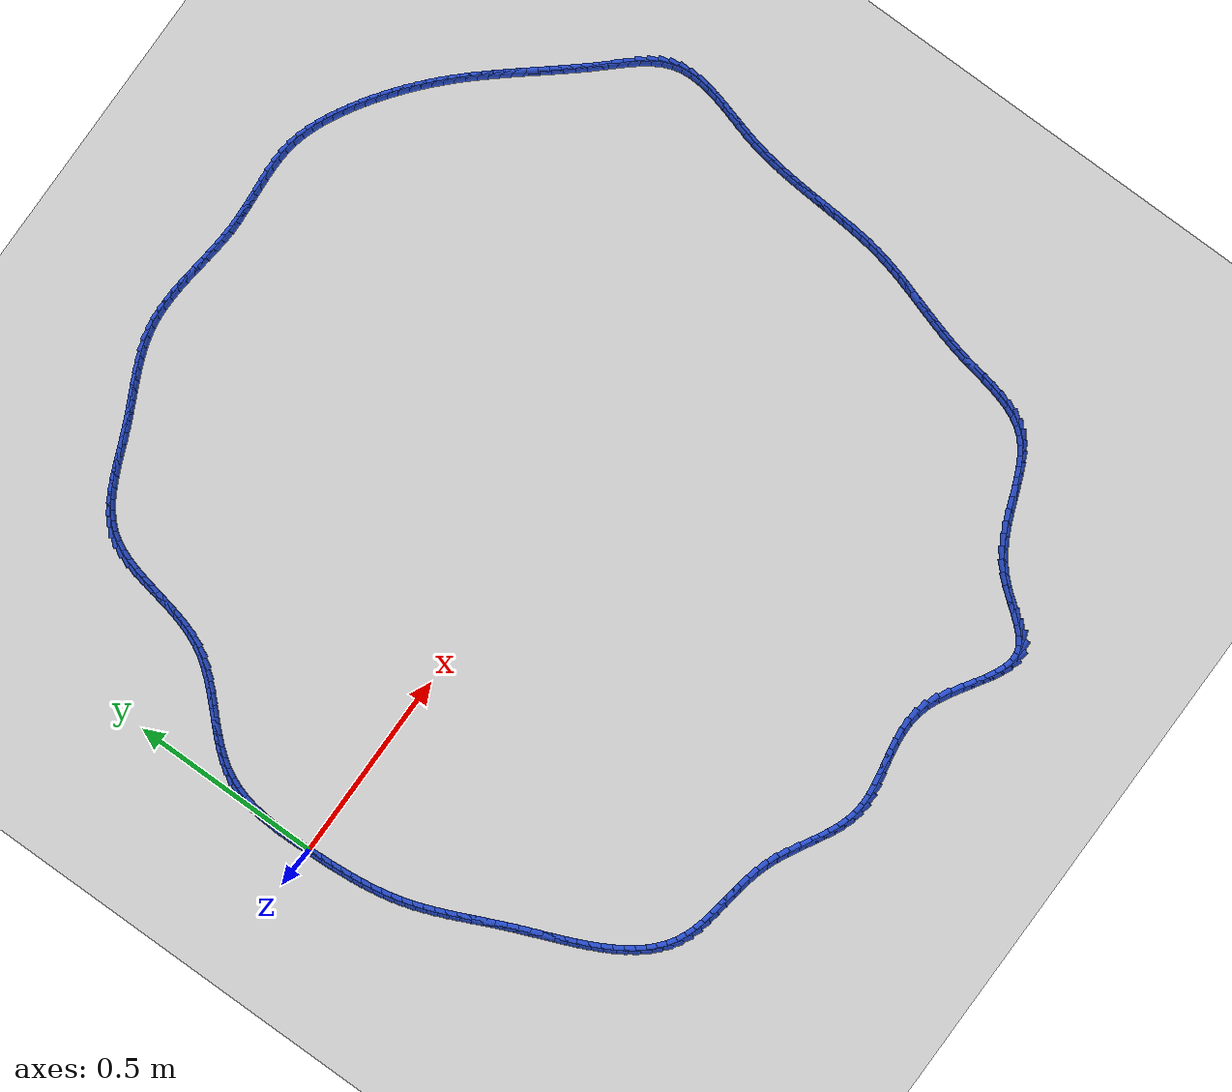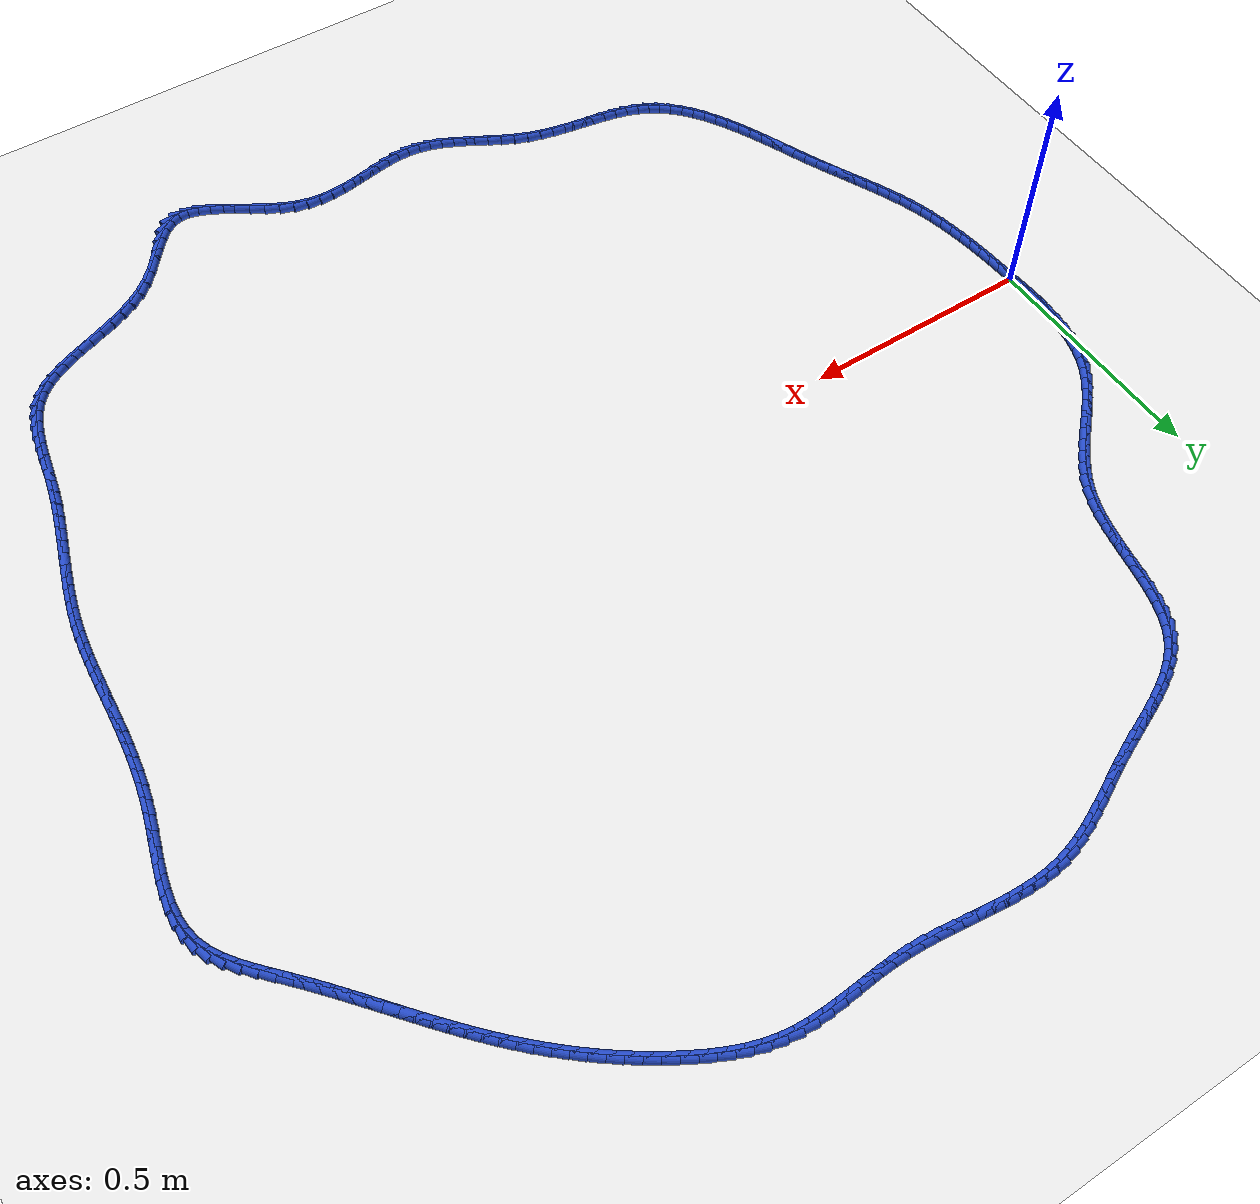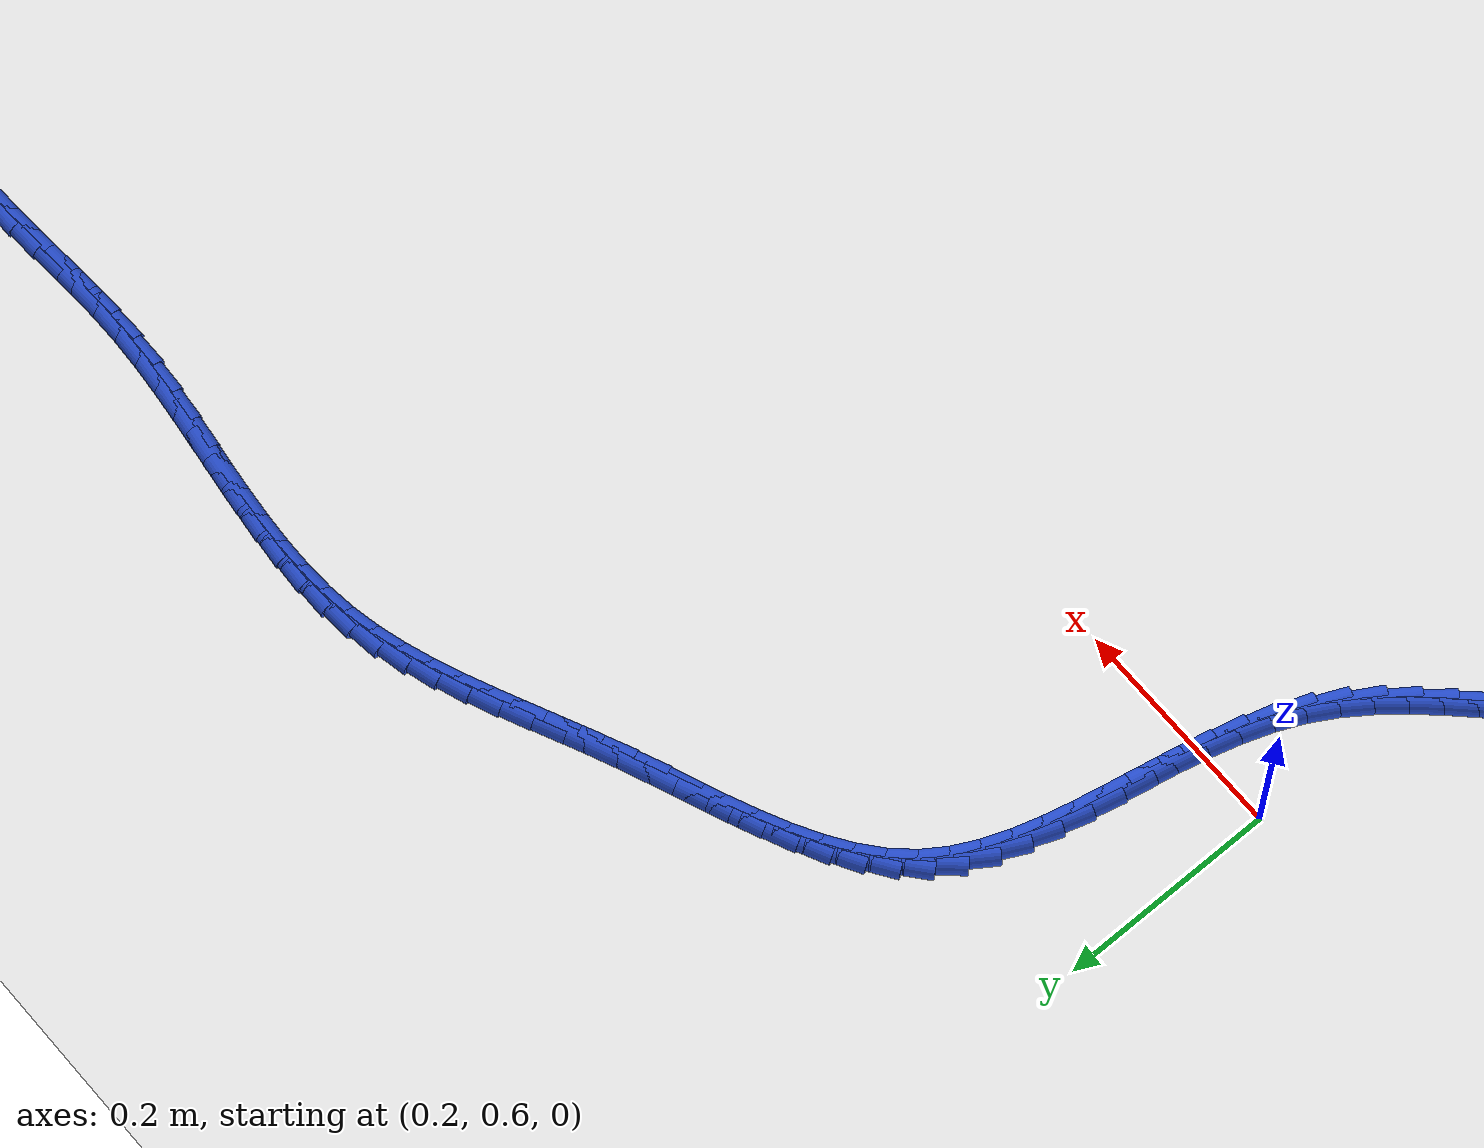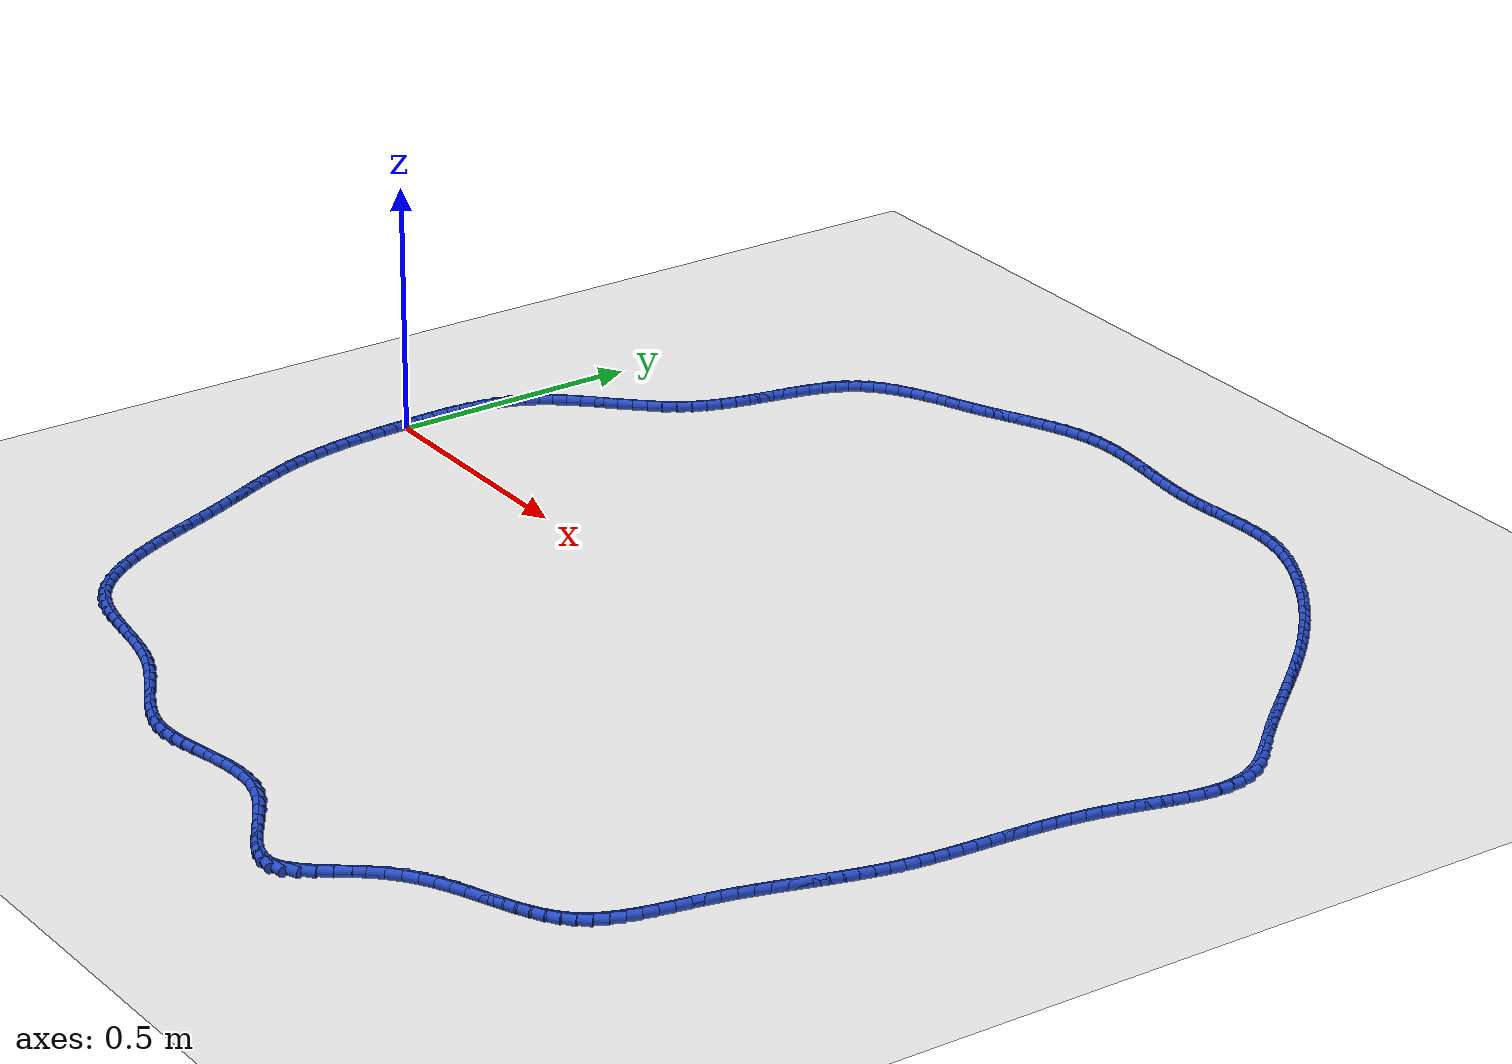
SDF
<sdf version="1.6">
 <world name="default">
  <light name="sun" type="directional">
   <pose>0 0 10 0 -0 0</pose>
   <diffuse>0.8 0.8 0.8 1</diffuse>
   <specular>0.2 0.2 0.2 1</specular>
   <attenuation>
    <range>1000</range>
    <constant>0.9</constant>
    <linear>0.01</linear>
    <quadratic>0.001</quadratic>
   </attenuation>
   <direction>-0.5 0.1 -0.9</direction>
  </light>
  <model name="ground_plane">
   <static>1</static>
   <link name="link">
    <collision name="collision">
     <geometry><plane><normal>0 0 1</normal><size>100 100</size></plane></geometry>
     <surface><friction><ode><mu>100</mu><mu2>50</mu2></ode></friction></surface>
    </collision>
    <visual name="visual">
     <cast_shadows>0</cast_shadows>
     <geometry><plane><normal>0 0 1</normal><size>100 100</size></plane></geometry>
     <material>
      <script><uri>file://media/materials/scripts/gazebo.material</uri><name>Gazebo/WhiteGlow</name></script>
     </material>
    </visual>
   </link>
  </model>
  <gravity>0 0 -9.8</gravity>
  <magnetic_field>6e-06 2.3e-05 -4.2e-05</magnetic_field>
  <atmosphere type="adiabatic"/>
  <physics name="default_physics" default="0" type="ode">
   <max_step_size>0.001</max_step_size>
   <real_time_factor>1</real_time_factor>
   <real_time_update_rate>1000</real_time_update_rate>
  </physics>
  <scene><ambient>0.4 0.4 0.4 1</ambient><background>0.7 0.7 0.7 1</background><shadows>1</shadows></scene>
  <spherical_coordinates>
   <surface_model>EARTH_WGS84</surface_model>
   <latitude_deg>0</latitude_deg>
   <longitude_deg>0</longitude_deg>
   <elevation>0</elevation>
   <heading_deg>0</heading_deg>
  </spherical_coordinates>
  <model name="line">
   <link name="link_0">
    <pose>-7.589415207398531e-19 -2.0816681711721685e-17 0.01 0 1.57 -1.5354599445000783</pose>
    <collision name="collision">
     <geometry><cylinder><radius>0.01</radius><length>0.08</length></cylinder></geometry>
    </collision>
    <visual name="visual">
     <material>
      <script><name>Gazebo/Blue</name><uri>file://media/materials/scripts/gazebo.material</uri></script>
     </material>
     <geometry><cylinder><radius>0.01</radius><length>0.08</length></cylinder></geometry>
    </visual>
   </link>
   <link name="link_1">
    <pose>-0.001038721061731485 0.029382993443548264 0.01 0 1.57 -1.5521858249136637</pose>
    <collision name="collision">
     <geometry><cylinder><radius>0.01</radius><length>0.08</length></cylinder></geometry>
    </collision>
    <visual name="visual">
     <material>
      <script><name>Gazebo/Blue</name><uri>file://media/materials/scripts/gazebo.material</uri></script>
     </material>
     <geometry><cylinder><radius>0.01</radius><length>0.08</length></cylinder></geometry>
    </visual>
   </link>
   <link name="link_2">
    <pose>-0.0015868101717463985 0.05883012146947917 0.01 0 1.57 1.5636319544767618</pose>
    <collision name="collision">
     <geometry><cylinder><radius>0.01</radius><length>0.08</length></cylinder></geometry>
    </collision>
    <visual name="visual">
     <material>
      <script><name>Gazebo/Blue</name><uri>file://media/materials/scripts/gazebo.material</uri></script>
     </material>
     <geometry><cylinder><radius>0.01</radius><length>0.08</length></cylinder></geometry>
    </visual>
   </link>
   <link name="link_3">
    <pose>-0.001376617637800966 0.08816820278761452 0.01 0 1.57 1.5282789411190123</pose>
    <collision name="collision">
     <geometry><cylinder><radius>0.01</radius><length>0.08</length></cylinder></geometry>
    </collision>
    <visual name="visual">
     <material>
      <script><name>Gazebo/Blue</name><uri>file://media/materials/scripts/gazebo.material</uri></script>
     </material>
     <geometry><cylinder><radius>0.01</radius><length>0.08</length></cylinder></geometry>
    </visual>
   </link>
   <link name="link_4">
    <pose>-0.00014049376765140923 0.11722405610777589 0.01 0 1.57 1.4825760618829906</pose>
    <collision name="collision">
     <geometry><cylinder><radius>0.01</radius><length>0.08</length></cylinder></geometry>
    </collision>
    <visual name="visual">
     <material>
      <script><name>Gazebo/Blue</name><uri>file://media/materials/scripts/gazebo.material</uri></script>
     </material>
     <geometry><cylinder><radius>0.01</radius><length>0.08</length></cylinder></geometry>
    </visual>
   </link>
   <link name="link_5">
    <pose>0.0023892111309460505 0.14582450013978498 0.01 0 1.57 1.425574041161223</pose>
    <collision name="collision">
     <geometry><cylinder><radius>0.01</radius><length>0.08</length></cylinder></geometry>
    </collision>
    <visual name="visual">
     <material>
      <script><name>Gazebo/Blue</name><uri>file://media/materials/scripts/gazebo.material</uri></script>
     </material>
     <geometry><cylinder><radius>0.01</radius><length>0.08</length></cylinder></geometry>
    </visual>
   </link>
   <link name="link_6">
    <pose>0.006480146750235195 0.1737963535934635 0.01 0 1.57 1.356269095207587</pose>
    <collision name="collision">
     <geometry><cylinder><radius>0.01</radius><length>0.08</length></cylinder></geometry>
    </collision>
    <visual name="visual">
     <material>
      <script><name>Gazebo/Blue</name><uri>file://media/materials/scripts/gazebo.material</uri></script>
     </material>
     <geometry><cylinder><radius>0.01</radius><length>0.08</length></cylinder></geometry>
    </visual>
   </link>
   <link name="link_7">
    <pose>0.012399962782459788 0.20096643517863302 0.01 0 1.57 1.2738218459556372</pose>
    <collision name="collision">
     <geometry><cylinder><radius>0.01</radius><length>0.08</length></cylinder></geometry>
    </collision>
    <visual name="visual">
     <material>
      <script><name>Gazebo/Blue</name><uri>file://media/materials/scripts/gazebo.material</uri></script>
     </material>
     <geometry><cylinder><radius>0.01</radius><length>0.08</length></cylinder></geometry>
    </visual>
   </link>
   <link name="link_8">
    <pose>0.020416308919863617 0.2271615636051153 0.01 0 1.57 1.177902288829453</pose>
    <collision name="collision">
     <geometry><cylinder><radius>0.01</radius><length>0.08</length></cylinder></geometry>
    </collision>
    <visual name="visual">
     <material>
      <script><name>Gazebo/Blue</name><uri>file://media/materials/scripts/gazebo.material</uri></script>
     </material>
     <geometry><cylinder><radius>0.01</radius><length>0.08</length></cylinder></geometry>
    </visual>
   </link>
   <link name="link_9">
    <pose>0.03079683485469047 0.2522085575827321 0.01 0 1.57 1.0711286488713487</pose>
    <collision name="collision">
     <geometry><cylinder><radius>0.01</radius><length>0.08</length></cylinder></geometry>
    </collision>
    <visual name="visual">
     <material>
      <script><name>Gazebo/Blue</name><uri>file://media/materials/scripts/gazebo.material</uri></script>
     </material>
     <geometry><cylinder><radius>0.01</radius><length>0.08</length></cylinder></geometry>
    </visual>
   </link>
   <link name="link_10">
    <pose>0.043762873604115037 0.27596149039614104 0.01 0 1.57 0.9739048108310363</pose>
    <collision name="collision">
     <geometry><cylinder><radius>0.01</radius><length>0.08</length></cylinder></geometry>
    </collision>
    <visual name="visual">
     <material>
      <script><name>Gazebo/Blue</name><uri>file://media/materials/scripts/gazebo.material</uri></script>
     </material>
     <geometry><cylinder><radius>0.01</radius><length>0.08</length></cylinder></geometry>
    </visual>
   </link>
   <link name="link_11">
    <pose>0.059100450473078915 0.29853058771144986 0.01 0 1.57 0.8975253995782075</pose>
    <collision name="collision">
     <geometry><cylinder><radius>0.01</radius><length>0.08</length></cylinder></geometry>
    </collision>
    <visual name="visual">
     <material>
      <script><name>Gazebo/Blue</name><uri>file://media/materials/scripts/gazebo.material</uri></script>
     </material>
     <geometry><cylinder><radius>0.01</radius><length>0.08</length></cylinder></geometry>
    </visual>
   </link>
   <link name="link_12">
    <pose>0.07635703975394408 0.32016644810398037 0.01 0 1.57 0.8416465950322856</pose>
    <collision name="collision">
     <geometry><cylinder><radius>0.01</radius><length>0.08</length></cylinder></geometry>
    </collision>
    <visual name="visual">
     <material>
      <script><name>Gazebo/Blue</name><uri>file://media/materials/scripts/gazebo.material</uri></script>
     </material>
     <geometry><cylinder><radius>0.01</radius><length>0.08</length></cylinder></geometry>
    </visual>
   </link>
   <link name="link_13">
    <pose>0.09507767091906177 0.3411211087784433 0.01 0 1.57 0.8051643546833973</pose>
    <collision name="collision">
     <geometry><cylinder><radius>0.01</radius><length>0.08</length></cylinder></geometry>
    </collision>
    <visual name="visual">
     <material>
      <script><name>Gazebo/Blue</name><uri>file://media/materials/scripts/gazebo.material</uri></script>
     </material>
     <geometry><cylinder><radius>0.01</radius><length>0.08</length></cylinder></geometry>
    </visual>
   </link>
   <link name="link_14">
    <pose>0.11480737344078334 0.36164660693954914 0.01 0 1.57 0.7869872844700521</pose>
    <collision name="collision">
     <geometry><cylinder><radius>0.01</radius><length>0.08</length></cylinder></geometry>
    </collision>
    <visual name="visual">
     <material>
      <script><name>Gazebo/Blue</name><uri>file://media/materials/scripts/gazebo.material</uri></script>
     </material>
     <geometry><cylinder><radius>0.01</radius><length>0.08</length></cylinder></geometry>
    </visual>
   </link>
   <link name="link_15">
    <pose>0.13509117679146 0.3819949797920085 0.01 0 1.57 0.7863870098274814</pose>
    <collision name="collision">
     <geometry><cylinder><radius>0.01</radius><length>0.08</length></cylinder></geometry>
    </collision>
    <visual name="visual">
     <material>
      <script><name>Gazebo/Blue</name><uri>file://media/materials/scripts/gazebo.material</uri></script>
     </material>
     <geometry><cylinder><radius>0.01</radius><length>0.08</length></cylinder></geometry>
    </visual>
   </link>
   <link name="link_16">
    <pose>0.15547411044344311 0.40241826454053214 0.01 0 1.57 0.8031301894841878</pose>
    <collision name="collision">
     <geometry><cylinder><radius>0.01</radius><length>0.08</length></cylinder></geometry>
    </collision>
    <visual name="visual">
     <material>
      <script><name>Gazebo/Blue</name><uri>file://media/materials/scripts/gazebo.material</uri></script>
     </material>
     <geometry><cylinder><radius>0.01</radius><length>0.08</length></cylinder></geometry>
    </visual>
   </link>
   <link name="link_17">
    <pose>0.17550120386908394 0.42316849838983056 0.01 0 1.57 0.8374638110827034</pose>
    <collision name="collision">
     <geometry><cylinder><radius>0.01</radius><length>0.08</length></cylinder></geometry>
    </collision>
    <visual name="visual">
     <material>
      <script><name>Gazebo/Blue</name><uri>file://media/materials/scripts/gazebo.material</uri></script>
     </material>
     <geometry><cylinder><radius>0.01</radius><length>0.08</length></cylinder></geometry>
    </visual>
   </link>
   <link name="link_18">
    <pose>0.19471748654073373 0.4444977185446144 0.01 0 1.57 0.8899683148135948</pose>
    <collision name="collision">
     <geometry><cylinder><radius>0.01</radius><length>0.08</length></cylinder></geometry>
    </collision>
    <visual name="visual">
     <material>
      <script><name>Gazebo/Blue</name><uri>file://media/materials/scripts/gazebo.material</uri></script>
     </material>
     <geometry><cylinder><radius>0.01</radius><length>0.08</length></cylinder></geometry>
    </visual>
   </link>
   <link name="link_19">
    <pose>0.21266798793074382 0.4666579622095942 0.01 0 1.57 0.9612425770427995</pose>
    <collision name="collision">
     <geometry><cylinder><radius>0.01</radius><length>0.08</length></cylinder></geometry>
    </collision>
    <visual name="visual">
     <material>
      <script><name>Gazebo/Blue</name><uri>file://media/materials/scripts/gazebo.material</uri></script>
     </material>
     <geometry><cylinder><radius>0.01</radius><length>0.08</length></cylinder></geometry>
    </visual>
   </link>
   <link name="link_20">
    <pose>0.22889773751146542 0.4899012665894805 0.01 0 1.57 1.0513671834905756</pose>
    <collision name="collision">
     <geometry><cylinder><radius>0.01</radius><length>0.08</length></cylinder></geometry>
    </collision>
    <visual name="visual">
     <material>
      <script><name>Gazebo/Blue</name><uri>file://media/materials/scripts/gazebo.material</uri></script>
     </material>
     <geometry><cylinder><radius>0.01</radius><length>0.08</length></cylinder></geometry>
    </visual>
   </link>
   <link name="link_21">
    <pose>0.24295176729041829 0.5144796673006181 0.01 0 1.57 1.1522957327211576</pose>
    <collision name="collision">
     <geometry><cylinder><radius>0.01</radius><length>0.08</length></cylinder></geometry>
    </collision>
    <visual name="visual">
     <material>
      <script><name>Gazebo/Blue</name><uri>file://media/materials/scripts/gazebo.material</uri></script>
     </material>
     <geometry><cylinder><radius>0.01</radius><length>0.08</length></cylinder></geometry>
    </visual>
   </link>
   <link name="link_22">
    <pose>0.2545428161926947 0.5405401260811693 0.01 0 1.57 1.2371412166204445</pose>
    <collision name="collision">
     <geometry><cylinder><radius>0.01</radius><length>0.08</length></cylinder></geometry>
    </collision>
    <visual name="visual">
     <material>
      <script><name>Gazebo/Blue</name><uri>file://media/materials/scripts/gazebo.material</uri></script>
     </material>
     <geometry><cylinder><radius>0.01</radius><length>0.08</length></cylinder></geometry>
    </visual>
   </link>
   <link name="link_23">
    <pose>0.26400535680978926 0.5678400681583937 0.01 0 1.57 1.300593996096483</pose>
    <collision name="collision">
     <geometry><cylinder><radius>0.01</radius><length>0.08</length></cylinder></geometry>
    </collision>
    <visual name="visual">
     <material>
      <script><name>Gazebo/Blue</name><uri>file://media/materials/scripts/gazebo.material</uri></script>
     </material>
     <geometry><cylinder><radius>0.01</radius><length>0.08</length></cylinder></geometry>
    </visual>
   </link>
   <link name="link_24">
    <pose>0.2718179076857716 0.5960466692511083 0.01 0 1.57 1.344015931490667</pose>
    <collision name="collision">
     <geometry><cylinder><radius>0.01</radius><length>0.08</length></cylinder></geometry>
    </collision>
    <visual name="visual">
     <material>
      <script><name>Gazebo/Blue</name><uri>file://media/materials/scripts/gazebo.material</uri></script>
     </material>
     <geometry><cylinder><radius>0.01</radius><length>0.08</length></cylinder></geometry>
    </visual>
   </link>
   <link name="link_25">
    <pose>0.27845898736471114 0.6248271050781291 0.01 0 1.57 1.3686397083301012</pose>
    <collision name="collision">
     <geometry><cylinder><radius>0.01</radius><length>0.08</length></cylinder></geometry>
    </collision>
    <visual name="visual">
     <material>
      <script><name>Gazebo/Blue</name><uri>file://media/materials/scripts/gazebo.material</uri></script>
     </material>
     <geometry><cylinder><radius>0.01</radius><length>0.08</length></cylinder></geometry>
    </visual>
   </link>
   <link name="link_26">
    <pose>0.2844071143906777 0.6538485513582731 0.01 0 1.57 1.3751374631966333</pose>
    <collision name="collision">
     <geometry><cylinder><radius>0.01</radius><length>0.08</length></cylinder></geometry>
    </collision>
    <visual name="visual">
     <material>
      <script><name>Gazebo/Blue</name><uri>file://media/materials/scripts/gazebo.material</uri></script>
     </material>
     <geometry><cylinder><radius>0.01</radius><length>0.08</length></cylinder></geometry>
    </visual>
   </link>
   <link name="link_27">
    <pose>0.29014080730774056 0.6827781838103563 0.01 0 1.57 1.3634100883695495</pose>
    <collision name="collision">
     <geometry><cylinder><radius>0.01</radius><length>0.08</length></cylinder></geometry>
    </collision>
    <visual name="visual">
     <material>
      <script><name>Gazebo/Blue</name><uri>file://media/materials/scripts/gazebo.material</uri></script>
     </material>
     <geometry><cylinder><radius>0.01</radius><length>0.08</length></cylinder></geometry>
    </visual>
   </link>
   <link name="link_28">
    <pose>0.2961385846599696 0.7112831781531954 0.01 0 1.57 1.3324939191332077</pose>
    <collision name="collision">
     <geometry><cylinder><radius>0.01</radius><length>0.08</length></cylinder></geometry>
    </collision>
    <visual name="visual">
     <material>
      <script><name>Gazebo/Blue</name><uri>file://media/materials/scripts/gazebo.material</uri></script>
     </material>
     <geometry><cylinder><radius>0.01</radius><length>0.08</length></cylinder></geometry>
    </visual>
   </link>
   <link name="link_29">
    <pose>0.30287896499143424 0.7390307101056068 0.01 0 1.57 1.2805676561580188</pose>
    <collision name="collision">
     <geometry><cylinder><radius>0.01</radius><length>0.08</length></cylinder></geometry>
    </collision>
    <visual name="visual">
     <material>
      <script><name>Gazebo/Blue</name><uri>file://media/materials/scripts/gazebo.material</uri></script>
     </material>
     <geometry><cylinder><radius>0.01</radius><length>0.08</length></cylinder></geometry>
    </visual>
   </link>
   <link name="link_30">
    <pose>0.31084046684620414 0.7656879553864073 0.01 0 1.57 1.2051525236272433</pose>
    <collision name="collision">
     <geometry><cylinder><radius>0.01</radius><length>0.08</length></cylinder></geometry>
    </collision>
    <visual name="visual">
     <material>
      <script><name>Gazebo/Blue</name><uri>file://media/materials/scripts/gazebo.material</uri></script>
     </material>
     <geometry><cylinder><radius>0.01</radius><length>0.08</length></cylinder></geometry>
    </visual>
   </link>
   <link name="link_31">
    <pose>0.32050160876834877 0.7909220897144129 0.01 0 1.57 1.1037402848397018</pose>
    <collision name="collision">
     <geometry><cylinder><radius>0.01</radius><length>0.08</length></cylinder></geometry>
    </collision>
    <visual name="visual">
     <material>
      <script><name>Gazebo/Blue</name><uri>file://media/materials/scripts/gazebo.material</uri></script>
     </material>
     <geometry><cylinder><radius>0.01</radius><length>0.08</length></cylinder></geometry>
    </visual>
   </link>
   <link name="link_32">
    <pose>0.3323409093019378 0.8144002888084403 0.01 0 1.57 0.9751831111092903</pose>
    <collision name="collision">
     <geometry><cylinder><radius>0.01</radius><length>0.08</length></cylinder></geometry>
    </collision>
    <visual name="visual">
     <material>
      <script><name>Gazebo/Blue</name><uri>file://media/materials/scripts/gazebo.material</uri></script>
     </material>
     <geometry><cylinder><radius>0.01</radius><length>0.08</length></cylinder></geometry>
    </visual>
   </link>
   <link name="link_33">
    <pose>0.3468368795343951 0.8357897339492958 0.01 0 1.57 0.8297698026181637</pose>
    <collision name="collision">
     <geometry><cylinder><radius>0.01</radius><length>0.08</length></cylinder></geometry>
    </collision>
    <visual name="visual">
     <material>
      <script><name>Gazebo/Blue</name><uri>file://media/materials/scripts/gazebo.material</uri></script>
     </material>
     <geometry><cylinder><radius>0.01</radius><length>0.08</length></cylinder></geometry>
    </visual>
   </link>
   <link name="link_34">
    <pose>0.36430395980754077 0.8548799884916853 0.01 0 1.57 0.7009818236331115</pose>
    <collision name="collision">
     <geometry><cylinder><radius>0.01</radius><length>0.08</length></cylinder></geometry>
    </collision>
    <visual name="visual">
     <material>
      <script><name>Gazebo/Blue</name><uri>file://media/materials/scripts/gazebo.material</uri></script>
     </material>
     <geometry><cylinder><radius>0.01</radius><length>0.08</length></cylinder></geometry>
    </visual>
   </link>
   <link name="link_35">
    <pose>0.38446916699355965 0.8718987810598613 0.01 0 1.57 0.5972072402549462</pose>
    <collision name="collision">
     <geometry><cylinder><radius>0.01</radius><length>0.08</length></cylinder></geometry>
    </collision>
    <visual name="visual">
     <material>
      <script><name>Gazebo/Blue</name><uri>file://media/materials/scripts/gazebo.material</uri></script>
     </material>
     <geometry><cylinder><radius>0.01</radius><length>0.08</length></cylinder></geometry>
    </visual>
   </link>
   <link name="link_36">
    <pose>0.4069281044457462 0.8871718629872495 0.01 0 1.57 0.5172810501137337</pose>
    <collision name="collision">
     <geometry><cylinder><radius>0.01</radius><length>0.08</length></cylinder></geometry>
    </collision>
    <visual name="visual">
     <material>
      <script><name>Gazebo/Blue</name><uri>file://media/materials/scripts/gazebo.material</uri></script>
     </material>
     <geometry><cylinder><radius>0.01</radius><length>0.08</length></cylinder></geometry>
    </visual>
   </link>
   <link name="link_37">
    <pose>0.4312763755173954 0.9010249856072765 0.01 0 1.57 0.4587523879835254</pose>
    <collision name="collision">
     <geometry><cylinder><radius>0.01</radius><length>0.08</length></cylinder></geometry>
    </collision>
    <visual name="visual">
     <material>
      <script><name>Gazebo/Blue</name><uri>file://media/materials/scripts/gazebo.material</uri></script>
     </material>
     <geometry><cylinder><radius>0.01</radius><length>0.08</length></cylinder></geometry>
    </visual>
   </link>
   <link name="link_38">
    <pose>0.45710958356180154 0.9137839002533681 0.01 0 1.57 0.41911730472576453</pose>
    <collision name="collision">
     <geometry><cylinder><radius>0.01</radius><length>0.08</length></cylinder></geometry>
    </collision>
    <visual name="visual">
     <material>
      <script><name>Gazebo/Blue</name><uri>file://media/materials/scripts/gazebo.material</uri></script>
     </material>
     <geometry><cylinder><radius>0.01</radius><length>0.08</length></cylinder></geometry>
    </visual>
   </link>
   <link name="link_39">
    <pose>0.4840233319322596 0.9257743582589505 0.01 0 1.57 0.39639488406100976</pose>
    <collision name="collision">
     <geometry><cylinder><radius>0.01</radius><length>0.08</length></cylinder></geometry>
    </collision>
    <visual name="visual">
     <material>
      <script><name>Gazebo/Blue</name><uri>file://media/materials/scripts/gazebo.material</uri></script>
     </material>
     <geometry><cylinder><radius>0.01</radius><length>0.08</length></cylinder></geometry>
    </visual>
   </link>
   <link name="link_40">
    <pose>0.5116132239820641 0.9373221109574503 0.01 0 1.57 0.38932847842116053</pose>
    <collision name="collision">
     <geometry><cylinder><radius>0.01</radius><length>0.08</length></cylinder></geometry>
    </collision>
    <visual name="visual">
     <material>
      <script><name>Gazebo/Blue</name><uri>file://media/materials/scripts/gazebo.material</uri></script>
     </material>
     <geometry><cylinder><radius>0.01</radius><length>0.08</length></cylinder></geometry>
    </visual>
   </link>
   <link name="link_41">
    <pose>0.5394748630645099 0.9487529096822932 0.01 0 1.57 0.39742627563807803</pose>
    <collision name="collision">
     <geometry><cylinder><radius>0.01</radius><length>0.08</length></cylinder></geometry>
    </collision>
    <visual name="visual">
     <material>
      <script><name>Gazebo/Blue</name><uri>file://media/materials/scripts/gazebo.material</uri></script>
     </material>
     <geometry><cylinder><radius>0.01</radius><length>0.08</length></cylinder></geometry>
    </visual>
   </link>
   <link name="link_42">
    <pose>0.5672038525328915 0.9603925057669058 0.01 0 1.57 0.418891159312501</pose>
    <collision name="collision">
     <geometry><cylinder><radius>0.01</radius><length>0.08</length></cylinder></geometry>
    </collision>
    <visual name="visual">
     <material>
      <script><name>Gazebo/Blue</name><uri>file://media/materials/scripts/gazebo.material</uri></script>
     </material>
     <geometry><cylinder><radius>0.01</radius><length>0.08</length></cylinder></geometry>
    </visual>
   </link>
   <link name="link_43">
    <pose>0.594435343726891 0.9725171428770415 0.01 0 1.57 0.4372875792906507</pose>
    <collision name="collision">
     <geometry><cylinder><radius>0.01</radius><length>0.08</length></cylinder></geometry>
    </collision>
    <visual name="visual">
     <material>
      <script><name>Gazebo/Blue</name><uri>file://media/materials/scripts/gazebo.material</uri></script>
     </material>
     <geometry><cylinder><radius>0.01</radius><length>0.08</length></cylinder></geometry>
    </visual>
   </link>
   <link name="link_44">
    <pose>0.6211296810498341 0.9849959756811436 0.01 0 1.57 0.4440868908183512</pose>
    <collision name="collision">
     <geometry><cylinder><radius>0.01</radius><length>0.08</length></cylinder></geometry>
    </collision>
    <visual name="visual">
     <material>
      <script><name>Gazebo/Blue</name><uri>file://media/materials/scripts/gazebo.material</uri></script>
     </material>
     <geometry><cylinder><radius>0.01</radius><length>0.08</length></cylinder></geometry>
    </visual>
   </link>
   <link name="link_45">
    <pose>0.647406914625069 0.9974982331767294 0.01 0 1.57 0.43880346209502574</pose>
    <collision name="collision">
     <geometry><cylinder><radius>0.01</radius><length>0.08</length></cylinder></geometry>
    </collision>
    <visual name="visual">
     <material>
      <script><name>Gazebo/Blue</name><uri>file://media/materials/scripts/gazebo.material</uri></script>
     </material>
     <geometry><cylinder><radius>0.01</radius><length>0.08</length></cylinder></geometry>
    </visual>
   </link>
   <link name="link_46">
    <pose>0.6733882002623637 1.009691760221167 0.01 0 1.57 0.4209097171881241</pose>
    <collision name="collision">
     <geometry><cylinder><radius>0.01</radius><length>0.08</length></cylinder></geometry>
    </collision>
    <visual name="visual">
     <material>
      <script><name>Gazebo/Blue</name><uri>file://media/materials/scripts/gazebo.material</uri></script>
     </material>
     <geometry><cylinder><radius>0.01</radius><length>0.08</length></cylinder></geometry>
    </visual>
   </link>
   <link name="link_47">
    <pose>0.6991946937714862 1.0212444016718247 0.01 0 1.57 0.38979277507109583</pose>
    <collision name="collision">
     <geometry><cylinder><radius>0.01</radius><length>0.08</length></cylinder></geometry>
    </collision>
    <visual name="visual">
     <material>
      <script><name>Gazebo/Blue</name><uri>file://media/materials/scripts/gazebo.material</uri></script>
     </material>
     <geometry><cylinder><radius>0.01</radius><length>0.08</length></cylinder></geometry>
    </visual>
   </link>
   <link name="link_48">
    <pose>0.7249475509622042 1.0318240023860696 0.01 0 1.57 0.3448377696085715</pose>
    <collision name="collision">
     <geometry><cylinder><radius>0.01</radius><length>0.08</length></cylinder></geometry>
    </collision>
    <visual name="visual">
     <material>
      <script><name>Gazebo/Blue</name><uri>file://media/materials/scripts/gazebo.material</uri></script>
     </material>
     <geometry><cylinder><radius>0.01</radius><length>0.08</length></cylinder></geometry>
    </visual>
   </link>
   <link name="link_49">
    <pose>0.7507679276442857 1.0410984072212695 0.01 0 1.57 0.285603122919033</pose>
    <collision name="collision">
     <geometry><cylinder><radius>0.01</radius><length>0.08</length></cylinder></geometry>
    </collision>
    <visual name="visual">
     <material>
      <script><name>Gazebo/Blue</name><uri>file://media/materials/scripts/gazebo.material</uri></script>
     </material>
     <geometry><cylinder><radius>0.01</radius><length>0.08</length></cylinder></geometry>
    </visual>
   </link>
   <link name="link_50">
    <pose>0.7767769796274986 1.0487354610347925 0.01 0 1.57 0.2121025445644821</pose>
    <collision name="collision">
     <geometry><cylinder><radius>0.01</radius><length>0.08</length></cylinder></geometry>
    </collision>
    <visual name="visual">
     <material>
      <script><name>Gazebo/Blue</name><uri>file://media/materials/scripts/gazebo.material</uri></script>
     </material>
     <geometry><cylinder><radius>0.01</radius><length>0.08</length></cylinder></geometry>
    </visual>
   </link>
   <link name="link_51">
    <pose>0.8030958627216108 1.0544030086840066 0.01 0 1.57 0.12846499892986996</pose>
    <collision name="collision">
     <geometry><cylinder><radius>0.01</radius><length>0.08</length></cylinder></geometry>
    </collision>
    <visual name="visual">
     <material>
      <script><name>Gazebo/Blue</name><uri>file://media/materials/scripts/gazebo.material</uri></script>
     </material>
     <geometry><cylinder><radius>0.01</radius><length>0.08</length></cylinder></geometry>
    </visual>
   </link>
   <link name="link_52">
    <pose>0.8298244922479258 1.0578557166184495 0.01 0 1.57 0.05291289589701586</pose>
    <collision name="collision">
     <geometry><cylinder><radius>0.01</radius><length>0.08</length></cylinder></geometry>
    </collision>
    <visual name="visual">
     <material>
      <script><name>Gazebo/Blue</name><uri>file://media/materials/scripts/gazebo.material</uri></script>
     </material>
     <geometry><cylinder><radius>0.01</radius><length>0.08</length></cylinder></geometry>
    </visual>
   </link>
   <link name="link_53">
    <pose>0.8569540847565095 1.0592925631217 0.01 0 1.57 -0.008668730914118777</pose>
    <collision name="collision">
     <geometry><cylinder><radius>0.01</radius><length>0.08</length></cylinder></geometry>
    </collision>
    <visual name="visual">
     <material>
      <script><name>Gazebo/Blue</name><uri>file://media/materials/scripts/gazebo.material</uri></script>
     </material>
     <geometry><cylinder><radius>0.01</radius><length>0.08</length></cylinder></geometry>
    </visual>
   </link>
   <link name="link_54">
    <pose>0.8844411777334026 1.05905427894027 0.01 0 1.57 -0.056506672630093666</pose>
    <collision name="collision">
     <geometry><cylinder><radius>0.01</radius><length>0.08</length></cylinder></geometry>
    </collision>
    <visual name="visual">
     <material>
      <script><name>Gazebo/Blue</name><uri>file://media/materials/scripts/gazebo.material</uri></script>
     </material>
     <geometry><cylinder><radius>0.01</radius><length>0.08</length></cylinder></geometry>
    </visual>
   </link>
   <link name="link_55">
    <pose>0.9122422936407425 1.0574816562316447 0.01 0 1.57 -0.09116156158491154</pose>
    <collision name="collision">
     <geometry><cylinder><radius>0.01</radius><length>0.08</length></cylinder></geometry>
    </collision>
    <visual name="visual">
     <material>
      <script><name>Gazebo/Blue</name><uri>file://media/materials/scripts/gazebo.material</uri></script>
     </material>
     <geometry><cylinder><radius>0.01</radius><length>0.08</length></cylinder></geometry>
    </visual>
   </link>
   <link name="link_56">
    <pose>0.9403139549406672 1.0549154871533113 0.01 0 1.57 -0.11326117406294703</pose>
    <collision name="collision">
     <geometry><cylinder><radius>0.01</radius><length>0.08</length></cylinder></geometry>
    </collision>
    <visual name="visual">
     <material>
      <script><name>Gazebo/Blue</name><uri>file://media/materials/scripts/gazebo.material</uri></script>
     </material>
     <geometry><cylinder><radius>0.01</radius><length>0.08</length></cylinder></geometry>
    </visual>
   </link>
   <link name="link_57">
    <pose>0.9686126840953139 1.051696563862756 0.01 0 1.57 -0.12333836808788057</pose>
    <collision name="collision">
     <geometry><cylinder><radius>0.01</radius><length>0.08</length></cylinder></geometry>
    </collision>
    <visual name="visual">
     <material>
      <script><name>Gazebo/Blue</name><uri>file://media/materials/scripts/gazebo.material</uri></script>
     </material>
     <geometry><cylinder><radius>0.01</radius><length>0.08</length></cylinder></geometry>
    </visual>
   </link>
   <link name="link_58">
    <pose>0.9970950035668208 1.048165678517466 0.01 0 1.57 -0.12174838325418057</pose>
    <collision name="collision">
     <geometry><cylinder><radius>0.01</radius><length>0.08</length></cylinder></geometry>
    </collision>
    <visual name="visual">
     <material>
      <script><name>Gazebo/Blue</name><uri>file://media/materials/scripts/gazebo.material</uri></script>
     </material>
     <geometry><cylinder><radius>0.01</radius><length>0.08</length></cylinder></geometry>
    </visual>
   </link>
   <link name="link_59">
    <pose>1.025717435817325 1.0446636232749276 0.01 0 1.57 -0.10864207669625411</pose>
    <collision name="collision">
     <geometry><cylinder><radius>0.01</radius><length>0.08</length></cylinder></geometry>
    </collision>
    <visual name="visual">
     <material>
      <script><name>Gazebo/Blue</name><uri>file://media/materials/scripts/gazebo.material</uri></script>
     </material>
     <geometry><cylinder><radius>0.01</radius><length>0.08</length></cylinder></geometry>
    </visual>
   </link>
   <link name="link_60">
    <pose>1.054436503308965 1.041531190292627 0.01 0 1.57 -0.08398105640327302</pose>
    <collision name="collision">
     <geometry><cylinder><radius>0.01</radius><length>0.08</length></cylinder></geometry>
    </collision>
    <visual name="visual">
     <material>
      <script><name>Gazebo/Blue</name><uri>file://media/materials/scripts/gazebo.material</uri></script>
     </material>
     <geometry><cylinder><radius>0.01</radius><length>0.08</length></cylinder></geometry>
    </visual>
   </link>
   <link name="link_61">
    <pose>1.0832087285038776 1.0391091717280514 0.01 0 1.57 -0.04759159864553037</pose>
    <collision name="collision">
     <geometry><cylinder><radius>0.01</radius><length>0.08</length></cylinder></geometry>
    </collision>
    <visual name="visual">
     <material>
      <script><name>Gazebo/Blue</name><uri>file://media/materials/scripts/gazebo.material</uri></script>
     </material>
     <geometry><cylinder><radius>0.01</radius><length>0.08</length></cylinder></geometry>
    </visual>
   </link>
   <link name="link_62">
    <pose>1.1119906338642012 1.0377383597386876 0.01 0 1.57 -0.0009077507735317246</pose>
    <collision name="collision">
     <geometry><cylinder><radius>0.01</radius><length>0.08</length></cylinder></geometry>
    </collision>
    <visual name="visual">
     <material>
      <script><name>Gazebo/Blue</name><uri>file://media/materials/scripts/gazebo.material</uri></script>
     </material>
     <geometry><cylinder><radius>0.01</radius><length>0.08</length></cylinder></geometry>
    </visual>
   </link>
   <link name="link_63">
    <pose>1.1407393812747322 1.0377122630338196 0.01 0 1.57 0.03935869559519546</pose>
    <collision name="collision">
     <geometry><cylinder><radius>0.01</radius><length>0.08</length></cylinder></geometry>
    </collision>
    <visual name="visual">
     <material>
      <script><name>Gazebo/Blue</name><uri>file://media/materials/scripts/gazebo.material</uri></script>
     </material>
     <geometry><cylinder><radius>0.01</radius><length>0.08</length></cylinder></geometry>
    </visual>
   </link>
   <link name="link_64">
    <pose>1.169418661139253 1.038841625307769 0.01 0 1.57 0.06336344936523843</pose>
    <collision name="collision">
     <geometry><cylinder><radius>0.01</radius><length>0.08</length></cylinder></geometry>
    </collision>
    <visual name="visual">
     <material>
      <script><name>Gazebo/Blue</name><uri>file://media/materials/scripts/gazebo.material</uri></script>
     </material>
     <geometry><cylinder><radius>0.01</radius><length>0.08</length></cylinder></geometry>
    </visual>
   </link>
   <link name="link_65">
    <pose>1.1979959825380984 1.0406548102164859 0.01 0 1.57 0.07096385921496393</pose>
    <collision name="collision">
     <geometry><cylinder><radius>0.01</radius><length>0.08</length></cylinder></geometry>
    </collision>
    <visual name="visual">
     <material>
      <script><name>Gazebo/Blue</name><uri>file://media/materials/scripts/gazebo.material</uri></script>
     </material>
     <geometry><cylinder><radius>0.01</radius><length>0.08</length></cylinder></geometry>
    </visual>
   </link>
   <link name="link_66">
    <pose>1.226438902651079 1.0426766245993333 0.01 0 1.57 0.06199592030524616</pose>
    <collision name="collision">
     <geometry><cylinder><radius>0.01</radius><length>0.08</length></cylinder></geometry>
    </collision>
    <visual name="visual">
     <material>
      <script><name>Gazebo/Blue</name><uri>file://media/materials/scripts/gazebo.material</uri></script>
     </material>
     <geometry><cylinder><radius>0.01</radius><length>0.08</length></cylinder></geometry>
    </visual>
   </link>
   <link name="link_67">
    <pose>1.254714978658005 1.0444318752956745 0.01 0 1.57 0.03608154739395848</pose>
    <collision name="collision">
     <geometry><cylinder><radius>0.01</radius><length>0.08</length></cylinder></geometry>
    </collision>
    <visual name="visual">
     <material>
      <script><name>Gazebo/Blue</name><uri>file://media/materials/scripts/gazebo.material</uri></script>
     </material>
     <geometry><cylinder><radius>0.01</radius><length>0.08</length></cylinder></geometry>
    </visual>
   </link>
   <link name="link_68">
    <pose>1.2827917677386875 1.0454453691448726 0.01 0 1.57 -0.007306593803092277</pose>
    <collision name="collision">
     <geometry><cylinder><radius>0.01</radius><length>0.08</length></cylinder></geometry>
    </collision>
    <visual name="visual">
     <material>
      <script><name>Gazebo/Blue</name><uri>file://media/materials/scripts/gazebo.material</uri></script>
     </material>
     <geometry><cylinder><radius>0.01</radius><length>0.08</length></cylinder></geometry>
    </visual>
   </link>
   <link name="link_69">
    <pose>1.310636827072937 1.04524191298629 0.01 0 1.57 -0.06862081937940018</pose>
    <collision name="collision">
     <geometry><cylinder><radius>0.01</radius><length>0.08</length></cylinder></geometry>
    </collision>
    <visual name="visual">
     <material>
      <script><name>Gazebo/Blue</name><uri>file://media/materials/scripts/gazebo.material</uri></script>
     </material>
     <geometry><cylinder><radius>0.01</radius><length>0.08</length></cylinder></geometry>
    </visual>
   </link>
   <link name="link_70">
    <pose>1.3382177138405649 1.0433463136592906 0.01 0 1.57 -0.1478247919482586</pose>
    <collision name="collision">
     <geometry><cylinder><radius>0.01</radius><length>0.08</length></cylinder></geometry>
    </collision>
    <visual name="visual">
     <material>
      <script><name>Gazebo/Blue</name><uri>file://media/materials/scripts/gazebo.material</uri></script>
     </material>
     <geometry><cylinder><radius>0.01</radius><length>0.08</length></cylinder></geometry>
    </visual>
   </link>
   <link name="link_71">
    <pose>1.3655019851712904 1.0392833841148497 0.01 0 1.57 -0.23852647990503897</pose>
    <collision name="collision">
     <geometry><cylinder><radius>0.01</radius><length>0.08</length></cylinder></geometry>
    </collision>
    <visual name="visual">
     <material>
      <script><name>Gazebo/Blue</name><uri>file://media/materials/scripts/gazebo.material</uri></script>
     </material>
     <geometry><cylinder><radius>0.01</radius><length>0.08</length></cylinder></geometry>
    </visual>
   </link>
   <link name="link_72">
    <pose>1.392455957001149 1.032729377595018 0.01 0 1.57 -0.3204761642376022</pose>
    <collision name="collision">
     <geometry><cylinder><radius>0.01</radius><length>0.08</length></cylinder></geometry>
    </collision>
    <visual name="visual">
     <material>
      <script><name>Gazebo/Blue</name><uri>file://media/materials/scripts/gazebo.material</uri></script>
     </material>
     <geometry><cylinder><radius>0.01</radius><length>0.08</length></cylinder></geometry>
    </visual>
   </link>
   <link name="link_73">
    <pose>1.4190414816199879 1.023905164903328 0.01 0 1.57 -0.3896927531819471</pose>
    <collision name="collision">
     <geometry><cylinder><radius>0.01</radius><length>0.08</length></cylinder></geometry>
    </collision>
    <visual name="visual">
     <material>
      <script><name>Gazebo/Blue</name><uri>file://media/materials/scripts/gazebo.material</uri></script>
     </material>
     <geometry><cylinder><radius>0.01</radius><length>0.08</length></cylinder></geometry>
    </visual>
   </link>
   <link name="link_74">
    <pose>1.4452194082709324 1.0131540003916313 0.01 0 1.57 -0.4470112089415383</pose>
    <collision name="collision">
     <geometry><cylinder><radius>0.01</radius><length>0.08</length></cylinder></geometry>
    </collision>
    <visual name="visual">
     <material>
      <script><name>Gazebo/Blue</name><uri>file://media/materials/scripts/gazebo.material</uri></script>
     </material>
     <geometry><cylinder><radius>0.01</radius><length>0.08</length></cylinder></geometry>
    </visual>
   </link>
   <link name="link_75">
    <pose>1.4709505861971077 1.0008191384117777 0.01 0 1.57 -0.49337904855811854</pose>
    <collision name="collision">
     <geometry><cylinder><radius>0.01</radius><length>0.08</length></cylinder></geometry>
    </collision>
    <visual name="visual">
     <material>
      <script><name>Gazebo/Blue</name><uri>file://media/materials/scripts/gazebo.material</uri></script>
     </material>
     <geometry><cylinder><radius>0.01</radius><length>0.08</length></cylinder></geometry>
    </visual>
   </link>
   <link name="link_76">
    <pose>1.4961958646416402 0.9872438333156192 0.01 0 1.57 -0.5298311746733485</pose>
    <collision name="collision">
     <geometry><cylinder><radius>0.01</radius><length>0.08</length></cylinder></geometry>
    </collision>
    <visual name="visual">
     <material>
      <script><name>Gazebo/Blue</name><uri>file://media/materials/scripts/gazebo.material</uri></script>
     </material>
     <geometry><cylinder><radius>0.01</radius><length>0.08</length></cylinder></geometry>
    </visual>
   </link>
   <link name="link_77">
    <pose>1.5209169150296276 0.9727649550797888 0.01 0 1.57 -0.5610235095188191</pose>
    <collision name="collision">
     <geometry><cylinder><radius>0.01</radius><length>0.08</length></cylinder></geometry>
    </collision>
    <visual name="visual">
     <material>
      <script><name>Gazebo/Blue</name><uri>file://media/materials/scripts/gazebo.material</uri></script>
     </material>
     <geometry><cylinder><radius>0.01</radius><length>0.08</length></cylinder></geometry>
    </visual>
   </link>
   <link name="link_78">
    <pose>1.5450943308547798 0.9575724407756209 0.01 0 1.57 -0.591149794140414</pose>
    <collision name="collision">
     <geometry><cylinder><radius>0.01</radius><length>0.08</length></cylinder></geometry>
    </collision>
    <visual name="visual">
     <material>
      <script><name>Gazebo/Blue</name><uri>file://media/materials/scripts/gazebo.material</uri></script>
     </material>
     <geometry><cylinder><radius>0.01</radius><length>0.08</length></cylinder></geometry>
    </visual>
   </link>
   <link name="link_79">
    <pose>1.5687276342835734 0.9417092432867996 0.01 0 1.57 -0.6203870181535343</pose>
    <collision name="collision">
     <geometry><cylinder><radius>0.01</radius><length>0.08</length></cylinder></geometry>
    </collision>
    <visual name="visual">
     <material>
      <script><name>Gazebo/Blue</name><uri>file://media/materials/scripts/gazebo.material</uri></script>
     </material>
     <geometry><cylinder><radius>0.01</radius><length>0.08</length></cylinder></geometry>
    </visual>
   </link>
   <link name="link_80">
    <pose>1.591817170985292 0.9252119208653217 0.01 0 1.57 -0.6487404334091267</pose>
    <collision name="collision">
     <geometry><cylinder><radius>0.01</radius><length>0.08</length></cylinder></geometry>
    </collision>
    <visual name="visual">
     <material>
      <script><name>Gazebo/Blue</name><uri>file://media/materials/scripts/gazebo.material</uri></script>
     </material>
     <geometry><cylinder><radius>0.01</radius><length>0.08</length></cylinder></geometry>
    </visual>
   </link>
   <link name="link_81">
    <pose>1.6143632866292168 0.9081170317631827 0.01 0 1.57 -0.6762208371847891</pose>
    <collision name="collision">
     <geometry><cylinder><radius>0.01</radius><length>0.08</length></cylinder></geometry>
    </collision>
    <visual name="visual">
     <material>
      <script><name>Gazebo/Blue</name><uri>file://media/materials/scripts/gazebo.material</uri></script>
     </material>
     <geometry><cylinder><radius>0.01</radius><length>0.08</length></cylinder></geometry>
    </visual>
   </link>
   <link name="link_82">
    <pose>1.636366326884631 0.8904611342323807 0.01 0 1.57 -0.7028438273933689</pose>
    <collision name="collision">
     <geometry><cylinder><radius>0.01</radius><length>0.08</length></cylinder></geometry>
    </collision>
    <visual name="visual">
     <material>
      <script><name>Gazebo/Blue</name><uri>file://media/materials/scripts/gazebo.material</uri></script>
     </material>
     <geometry><cylinder><radius>0.01</radius><length>0.08</length></cylinder></geometry>
    </visual>
   </link>
   <link name="link_83">
    <pose>1.6578266374208153 0.8722807865249109 0.01 0 1.57 -0.7286290986854383</pose>
    <collision name="collision">
     <geometry><cylinder><radius>0.01</radius><length>0.08</length></cylinder></geometry>
    </collision>
    <visual name="visual">
     <material>
      <script><name>Gazebo/Blue</name><uri>file://media/materials/scripts/gazebo.material</uri></script>
     </material>
     <geometry><cylinder><radius>0.01</radius><length>0.08</length></cylinder></geometry>
    </visual>
   </link>
   <link name="link_84">
    <pose>1.6787445639070528 0.8536125468927701 0.01 0 1.57 -0.7535997923402684</pose>
    <collision name="collision">
     <geometry><cylinder><radius>0.01</radius><length>0.08</length></cylinder></geometry>
    </collision>
    <visual name="visual">
     <material>
      <script><name>Gazebo/Blue</name><uri>file://media/materials/scripts/gazebo.material</uri></script>
     </material>
     <geometry><cylinder><radius>0.01</radius><length>0.08</length></cylinder></geometry>
    </visual>
   </link>
   <link name="link_85">
    <pose>1.6991204520126255 0.8344929735879547 0.01 0 1.57 -0.7777818282216591</pose>
    <collision name="collision">
     <geometry><cylinder><radius>0.01</radius><length>0.08</length></cylinder></geometry>
    </collision>
    <visual name="visual">
     <material>
      <script><name>Gazebo/Blue</name><uri>file://media/materials/scripts/gazebo.material</uri></script>
     </material>
     <geometry><cylinder><radius>0.01</radius><length>0.08</length></cylinder></geometry>
    </visual>
   </link>
   <link name="link_86">
    <pose>1.7189546506634037 0.8149586247879211 0.01 0 1.57 -0.8007733322936967</pose>
    <collision name="collision">
     <geometry><cylinder><radius>0.01</radius><length>0.08</length></cylinder></geometry>
    </collision>
    <visual name="visual">
     <material>
      <script><name>Gazebo/Blue</name><uri>file://media/materials/scripts/gazebo.material</uri></script>
     </material>
     <geometry><cylinder><radius>0.01</radius><length>0.08</length></cylinder></geometry>
    </visual>
   </link>
   <link name="link_87">
    <pose>1.7382645009375504 0.7950456697326854 0.01 0 1.57 -0.8211030467952494</pose>
    <collision name="collision">
     <geometry><cylinder><radius>0.01</radius><length>0.08</length></cylinder></geometry>
    </collision>
    <visual name="visual">
     <material>
      <script><name>Gazebo/Blue</name><uri>file://media/materials/scripts/gazebo.material</uri></script>
     </material>
     <geometry><cylinder><radius>0.01</radius><length>0.08</length></cylinder></geometry>
    </visual>
   </link>
   <link name="link_88">
    <pose>1.7571239576715256 0.7747889818164057 0.01 0 1.57 -0.8383693134948366</pose>
    <collision name="collision">
     <geometry><cylinder><radius>0.01</radius><length>0.08</length></cylinder></geometry>
    </collision>
    <visual name="visual">
     <material>
      <script><name>Gazebo/Blue</name><uri>file://media/materials/scripts/gazebo.material</uri></script>
     </material>
     <geometry><cylinder><radius>0.01</radius><length>0.08</length></cylinder></geometry>
    </visual>
   </link>
   <link name="link_89">
    <pose>1.7756187516930626 0.7542231648897583 0.01 0 1.57 -0.8524948099996241</pose>
    <collision name="collision">
     <geometry><cylinder><radius>0.01</radius><length>0.08</length></cylinder></geometry>
    </collision>
    <visual name="visual">
     <material>
      <script><name>Gazebo/Blue</name><uri>file://media/materials/scripts/gazebo.material</uri></script>
     </material>
     <geometry><cylinder><radius>0.01</radius><length>0.08</length></cylinder></geometry>
    </visual>
   </link>
   <link name="link_90">
    <pose>1.7938346138298922 0.7333828228034208 0.01 0 1.57 -0.8634330793332667</pose>
    <collision name="collision">
     <geometry><cylinder><radius>0.01</radius><length>0.08</length></cylinder></geometry>
    </collision>
    <visual name="visual">
     <material>
      <script><name>Gazebo/Blue</name><uri>file://media/materials/scripts/gazebo.material</uri></script>
     </material>
     <geometry><cylinder><radius>0.01</radius><length>0.08</length></cylinder></geometry>
    </visual>
   </link>
   <link name="link_91">
    <pose>1.8118572749097475 0.7123025594080693 0.01 0 1.57 -0.8711648889584206</pose>
    <collision name="collision">
     <geometry><cylinder><radius>0.01</radius><length>0.08</length></cylinder></geometry>
    </collision>
    <visual name="visual">
     <material>
      <script><name>Gazebo/Blue</name><uri>file://media/materials/scripts/gazebo.material</uri></script>
     </material>
     <geometry><cylinder><radius>0.01</radius><length>0.08</length></cylinder></geometry>
    </visual>
   </link>
   <link name="link_92">
    <pose>1.8297724657603596 0.6910169785543804 0.01 0 1.57 -0.8756949224587817</pose>
    <collision name="collision">
     <geometry><cylinder><radius>0.01</radius><length>0.08</length></cylinder></geometry>
    </collision>
    <visual name="visual">
     <material>
      <script><name>Gazebo/Blue</name><uri>file://media/materials/scripts/gazebo.material</uri></script>
     </material>
     <geometry><cylinder><radius>0.01</radius><length>0.08</length></cylinder></geometry>
    </visual>
   </link>
   <link name="link_93">
    <pose>1.8476659172094614 0.6695606840930308 0.01 0 1.57 -0.8770490332902481</pose>
    <collision name="collision">
     <geometry><cylinder><radius>0.01</radius><length>0.08</length></cylinder></geometry>
    </collision>
    <visual name="visual">
     <material>
      <script><name>Gazebo/Blue</name><uri>file://media/materials/scripts/gazebo.material</uri></script>
     </material>
     <geometry><cylinder><radius>0.01</radius><length>0.08</length></cylinder></geometry>
    </visual>
   </link>
   <link name="link_94">
    <pose>1.865623360084784 0.6479682798746976 0.01 0 1.57 -0.8752721843655302</pose>
    <collision name="collision">
     <geometry><cylinder><radius>0.01</radius><length>0.08</length></cylinder></geometry>
    </collision>
    <visual name="visual">
     <material>
      <script><name>Gazebo/Blue</name><uri>file://media/materials/scripts/gazebo.material</uri></script>
     </material>
     <geometry><cylinder><radius>0.01</radius><length>0.08</length></cylinder></geometry>
    </visual>
   </link>
   <link name="link_95">
    <pose>1.8837305252140601 0.6262743697500572 0.01 0 1.57 -0.8704271049471141</pose>
    <collision name="collision">
     <geometry><cylinder><radius>0.01</radius><length>0.08</length></cylinder></geometry>
    </collision>
    <visual name="visual">
     <material>
      <script><name>Gazebo/Blue</name><uri>file://media/materials/scripts/gazebo.material</uri></script>
     </material>
     <geometry><cylinder><radius>0.01</radius><length>0.08</length></cylinder></geometry>
    </visual>
   </link>
   <link name="link_96">
    <pose>1.9020731434250218 0.604513557569786 0.01 0 1.57 -0.8625936191770527</pose>
    <collision name="collision">
     <geometry><cylinder><radius>0.01</radius><length>0.08</length></cylinder></geometry>
    </collision>
    <visual name="visual">
     <material>
      <script><name>Gazebo/Blue</name><uri>file://media/materials/scripts/gazebo.material</uri></script>
     </material>
     <geometry><cylinder><radius>0.01</radius><length>0.08</length></cylinder></geometry>
    </visual>
   </link>
   <link name="link_97">
    <pose>1.9207369455453995 0.582720447184561 0.01 0 1.57 -0.8518685377468678</pose>
    <collision name="collision">
     <geometry><cylinder><radius>0.01</radius><length>0.08</length></cylinder></geometry>
    </collision>
    <visual name="visual">
     <material>
      <script><name>Gazebo/Blue</name><uri>file://media/materials/scripts/gazebo.material</uri></script>
     </material>
     <geometry><cylinder><radius>0.01</radius><length>0.08</length></cylinder></geometry>
    </visual>
   </link>
   <link name="link_98">
    <pose>1.9398076624029272 0.5609296424450586 0.01 0 1.57 -0.8383659542039874</pose>
    <collision name="collision">
     <geometry><cylinder><radius>0.01</radius><length>0.08</length></cylinder></geometry>
    </collision>
    <visual name="visual">
     <material>
      <script><name>Gazebo/Blue</name><uri>file://media/materials/scripts/gazebo.material</uri></script>
     </material>
     <geometry><cylinder><radius>0.01</radius><length>0.08</length></cylinder></geometry>
    </visual>
   </link>
   <link name="link_99">
    <pose>1.9593710248253355 0.5391757472019557 0.01 0 1.57 -0.8256433552662915</pose>
    <collision name="collision">
     <geometry><cylinder><radius>0.01</radius><length>0.08</length></cylinder></geometry>
    </collision>
    <visual name="visual">
     <material>
      <script><name>Gazebo/Blue</name><uri>file://media/materials/scripts/gazebo.material</uri></script>
     </material>
     <geometry><cylinder><radius>0.01</radius><length>0.08</length></cylinder></geometry>
    </visual>
   </link>
   <link name="link_100">
    <pose>1.9794004942073467 0.5174655493958903 0.01 0 1.57 -0.8328999978954689</pose>
    <collision name="collision">
     <geometry><cylinder><radius>0.01</radius><length>0.08</length></cylinder></geometry>
    </collision>
    <visual name="visual">
     <material>
      <script><name>Gazebo/Blue</name><uri>file://media/materials/scripts/gazebo.material</uri></script>
     </material>
     <geometry><cylinder><radius>0.01</radius><length>0.08</length></cylinder></geometry>
    </visual>
   </link>
   <link name="link_101">
    <pose>1.9992368773855778 0.4956490902751773 0.01 0 1.57 -0.8675028361013063</pose>
    <collision name="collision">
     <geometry><cylinder><radius>0.01</radius><length>0.08</length></cylinder></geometry>
    </collision>
    <visual name="visual">
     <material>
      <script><name>Gazebo/Blue</name><uri>file://media/materials/scripts/gazebo.material</uri></script>
     </material>
     <geometry><cylinder><radius>0.01</radius><length>0.08</length></cylinder></geometry>
    </visual>
   </link>
   <link name="link_102">
    <pose>2.0179995701783637 0.47352155422459424 0.01 0 1.57 -0.9322442200639983</pose>
    <collision name="collision">
     <geometry><cylinder><radius>0.01</radius><length>0.08</length></cylinder></geometry>
    </collision>
    <visual name="visual">
     <material>
      <script><name>Gazebo/Blue</name><uri>file://media/materials/scripts/gazebo.material</uri></script>
     </material>
     <geometry><cylinder><radius>0.01</radius><length>0.08</length></cylinder></geometry>
    </visual>
   </link>
   <link name="link_103">
    <pose>2.0348077334677885 0.4508780674210389 0.01 0 1.57 -1.0318191896629265</pose>
    <collision name="collision">
     <geometry><cylinder><radius>0.01</radius><length>0.08</length></cylinder></geometry>
    </collision>
    <visual name="visual">
     <material>
      <script><name>Gazebo/Blue</name><uri>file://media/materials/scripts/gazebo.material</uri></script>
     </material>
     <geometry><cylinder><radius>0.01</radius><length>0.08</length></cylinder></geometry>
    </visual>
   </link>
   <link name="link_104">
    <pose>2.0487805281359344 0.4275137560414088 0.01 0 1.57 -1.1712235007734189</pose>
    <collision name="collision">
     <geometry><cylinder><radius>0.01</radius><length>0.08</length></cylinder></geometry>
    </collision>
    <visual name="visual">
     <material>
      <script><name>Gazebo/Blue</name><uri>file://media/materials/scripts/gazebo.material</uri></script>
     </material>
     <geometry><cylinder><radius>0.01</radius><length>0.08</length></cylinder></geometry>
    </visual>
   </link>
   <link name="link_105">
    <pose>2.0590378778197485 0.40322391940936164 0.01 0 1.57 -1.3371737413123586</pose>
    <collision name="collision">
     <geometry><cylinder><radius>0.01</radius><length>0.08</length></cylinder></geometry>
    </collision>
    <visual name="visual">
     <material>
      <script><name>Gazebo/Blue</name><uri>file://media/materials/scripts/gazebo.material</uri></script>
     </material>
     <geometry><cylinder><radius>0.01</radius><length>0.08</length></cylinder></geometry>
    </visual>
   </link>
   <link name="link_106">
    <pose>2.0650671836213066 0.3778872749100724 0.01 0 1.57 -1.4856037121164003</pose>
    <collision name="collision">
     <geometry><cylinder><radius>0.01</radius><length>0.08</length></cylinder></geometry>
    </collision>
    <visual name="visual">
     <material>
      <script><name>Gazebo/Blue</name><uri>file://media/materials/scripts/gazebo.material</uri></script>
     </material>
     <geometry><cylinder><radius>0.01</radius><length>0.08</length></cylinder></geometry>
    </visual>
   </link>
   <link name="link_107">
    <pose>2.067312131559645 0.3515996183664494 0.01 0 1.57 1.5360547349672506</pose>
    <collision name="collision">
     <geometry><cylinder><radius>0.01</radius><length>0.08</length></cylinder></geometry>
    </collision>
    <visual name="visual">
     <material>
      <script><name>Gazebo/Blue</name><uri>file://media/materials/scripts/gazebo.material</uri></script>
     </material>
     <geometry><cylinder><radius>0.01</radius><length>0.08</length></cylinder></geometry>
    </visual>
   </link>
   <link name="link_108">
    <pose>2.066369976979108 0.3244916061211365 0.01 0 1.57 1.444412673435188</pose>
    <collision name="collision">
     <geometry><cylinder><radius>0.01</radius><length>0.08</length></cylinder></geometry>
    </collision>
    <visual name="visual">
     <material>
      <script><name>Gazebo/Blue</name><uri>file://media/materials/scripts/gazebo.material</uri></script>
     </material>
     <geometry><cylinder><radius>0.01</radius><length>0.08</length></cylinder></geometry>
    </visual>
   </link>
   <link name="link_109">
    <pose>2.062837975224038 0.29669389451677847 0.01 0 1.57 1.378382022537058</pose>
    <collision name="collision">
     <geometry><cylinder><radius>0.01</radius><length>0.08</length></cylinder></geometry>
    </collision>
    <visual name="visual">
     <material>
      <script><name>Gazebo/Blue</name><uri>file://media/materials/scripts/gazebo.material</uri></script>
     </material>
     <geometry><cylinder><radius>0.01</radius><length>0.08</length></cylinder></geometry>
    </visual>
   </link>
   <link name="link_110">
    <pose>2.0573133816387785 0.26833713989601954 0.01 0 1.57 1.3348737533399988</pose>
    <collision name="collision">
     <geometry><cylinder><radius>0.01</radius><length>0.08</length></cylinder></geometry>
    </collision>
    <visual name="visual">
     <material>
      <script><name>Gazebo/Blue</name><uri>file://media/materials/scripts/gazebo.material</uri></script>
     </material>
     <geometry><cylinder><radius>0.01</radius><length>0.08</length></cylinder></geometry>
    </visual>
   </link>
   <link name="link_111">
    <pose>2.050393451567672 0.2395519986015037 0.01 0 1.57 1.3113956046576087</pose>
    <collision name="collision">
     <geometry><cylinder><radius>0.01</radius><length>0.08</length></cylinder></geometry>
    </collision>
    <visual name="visual">
     <material>
      <script><name>Gazebo/Blue</name><uri>file://media/materials/scripts/gazebo.material</uri></script>
     </material>
     <geometry><cylinder><radius>0.01</radius><length>0.08</length></cylinder></geometry>
    </visual>
   </link>
   <link name="link_112">
    <pose>2.0426754403550618 0.21046912697587497 0.01 0 1.57 1.3064042429006386</pose>
    <collision name="collision">
     <geometry><cylinder><radius>0.01</radius><length>0.08</length></cylinder></geometry>
    </collision>
    <visual name="visual">
     <material>
      <script><name>Gazebo/Blue</name><uri>file://media/materials/scripts/gazebo.material</uri></script>
     </material>
     <geometry><cylinder><radius>0.01</radius><length>0.08</length></cylinder></geometry>
    </visual>
   </link>
   <link name="link_113">
    <pose>2.0347566033452904 0.18121918136177825 0.01 0 1.57 1.3193744996362684</pose>
    <collision name="collision">
     <geometry><cylinder><radius>0.01</radius><length>0.08</length></cylinder></geometry>
    </collision>
    <visual name="visual">
     <material>
      <script><name>Gazebo/Blue</name><uri>file://media/materials/scripts/gazebo.material</uri></script>
     </material>
     <geometry><cylinder><radius>0.01</radius><length>0.08</length></cylinder></geometry>
    </visual>
   </link>
   <link name="link_114">
    <pose>2.027234195882701 0.15193281810185744 0.01 0 1.57 1.350084288263122</pose>
    <collision name="collision">
     <geometry><cylinder><radius>0.01</radius><length>0.08</length></cylinder></geometry>
    </collision>
    <visual name="visual">
     <material>
      <script><name>Gazebo/Blue</name><uri>file://media/materials/scripts/gazebo.material</uri></script>
     </material>
     <geometry><cylinder><radius>0.01</radius><length>0.08</length></cylinder></geometry>
    </visual>
   </link>
   <link name="link_115">
    <pose>2.0206836045051695 0.12273696500914132 0.01 0 1.57 1.3872837000156666</pose>
    <collision name="collision">
     <geometry><cylinder><radius>0.01</radius><length>0.08</length></cylinder></geometry>
    </collision>
    <visual name="visual">
     <material>
      <script><name>Gazebo/Blue</name><uri>file://media/materials/scripts/gazebo.material</uri></script>
     </material>
     <geometry><cylinder><radius>0.01</radius><length>0.08</length></cylinder></geometry>
    </visual>
   </link>
   <link name="link_116">
    <pose>2.015292932096982 0.09369251983809475 0.01 0 1.57 1.4205010767851265</pose>
    <collision name="collision">
     <geometry><cylinder><radius>0.01</radius><length>0.08</length></cylinder></geometry>
    </collision>
    <visual name="visual">
     <material>
      <script><name>Gazebo/Blue</name><uri>file://media/materials/scripts/gazebo.material</uri></script>
     </material>
     <geometry><cylinder><radius>0.01</radius><length>0.08</length></cylinder></geometry>
    </visual>
   </link>
   <link name="link_117">
    <pose>2.010918096073409 0.06480374426838093 0.01 0 1.57 1.449097660556877</pose>
    <collision name="collision">
     <geometry><cylinder><radius>0.01</radius><length>0.08</length></cylinder></geometry>
    </collision>
    <visual name="visual">
     <material>
      <script><name>Gazebo/Blue</name><uri>file://media/materials/scripts/gazebo.material</uri></script>
     </material>
     <geometry><cylinder><radius>0.01</radius><length>0.08</length></cylinder></geometry>
    </visual>
   </link>
   <link name="link_118">
    <pose>2.0074042460995414 0.03607306412842457 0.01 0 1.57 1.4728365128259158</pose>
    <collision name="collision">
     <geometry><cylinder><radius>0.01</radius><length>0.08</length></cylinder></geometry>
    </collision>
    <visual name="visual">
     <material>
      <script><name>Gazebo/Blue</name><uri>file://media/materials/scripts/gazebo.material</uri></script>
     </material>
     <geometry><cylinder><radius>0.01</radius><length>0.08</length></cylinder></geometry>
    </visual>
   </link>
   <link name="link_119">
    <pose>2.0045965318404635 0.007502905246649858 0.01 0 1.57 1.4915312010731696</pose>
    <collision name="collision">
     <geometry><cylinder><radius>0.01</radius><length>0.08</length></cylinder></geometry>
    </collision>
    <visual name="visual">
     <material>
      <script><name>Gazebo/Blue</name><uri>file://media/materials/scripts/gazebo.material</uri></script>
     </material>
     <geometry><cylinder><radius>0.01</radius><length>0.08</length></cylinder></geometry>
    </visual>
   </link>
   <link name="link_120">
    <pose>2.002340102961264 -0.020904306548517677 0.01 0 1.57 1.505031785290239</pose>
    <collision name="collision">
     <geometry><cylinder><radius>0.01</radius><length>0.08</length></cylinder></geometry>
    </collision>
    <visual name="visual">
     <material>
      <script><name>Gazebo/Blue</name><uri>file://media/materials/scripts/gazebo.material</uri></script>
     </material>
     <geometry><cylinder><radius>0.01</radius><length>0.08</length></cylinder></geometry>
    </visual>
   </link>
   <link name="link_121">
    <pose>2.0004801091270297 -0.04914614542865376 0.01 0 1.57 1.5132121716717142</pose>
    <collision name="collision">
     <geometry><cylinder><radius>0.01</radius><length>0.08</length></cylinder></geometry>
    </collision>
    <visual name="visual">
     <material>
      <script><name>Gazebo/Blue</name><uri>file://media/materials/scripts/gazebo.material</uri></script>
     </material>
     <geometry><cylinder><radius>0.01</radius><length>0.08</length></cylinder></geometry>
    </visual>
   </link>
   <link name="link_122">
    <pose>1.9988617000028492 -0.0772201855653338 0.01 0 1.57 1.5159601276195291</pose>
    <collision name="collision">
     <geometry><cylinder><radius>0.01</radius><length>0.08</length></cylinder></geometry>
    </collision>
    <visual name="visual">
     <material>
      <script><name>Gazebo/Blue</name><uri>file://media/materials/scripts/gazebo.material</uri></script>
     </material>
     <geometry><cylinder><radius>0.01</radius><length>0.08</length></cylinder></geometry>
    </visual>
   </link>
   <link name="link_123">
    <pose>1.99733002525381 -0.10512400113013314 0.01 0 1.57 1.5131709257031312</pose>
    <collision name="collision">
     <geometry><cylinder><radius>0.01</radius><length>0.08</length></cylinder></geometry>
    </collision>
    <visual name="visual">
     <material>
      <script><name>Gazebo/Blue</name><uri>file://media/materials/scripts/gazebo.material</uri></script>
     </material>
     <geometry><cylinder><radius>0.01</radius><length>0.08</length></cylinder></geometry>
    </visual>
   </link>
   <link name="link_124">
    <pose>1.9957302345449979 -0.13285516629462701 0.01 0 1.57 1.5047453895057048</pose>
    <collision name="collision">
     <geometry><cylinder><radius>0.01</radius><length>0.08</length></cylinder></geometry>
    </collision>
    <visual name="visual">
     <material>
      <script><name>Gazebo/Blue</name><uri>file://media/materials/scripts/gazebo.material</uri></script>
     </material>
     <geometry><cylinder><radius>0.01</radius><length>0.08</length></cylinder></geometry>
    </visual>
   </link>
   <link name="link_125">
    <pose>1.9939074775415024 -0.16041125523039163 0.01 0 1.57 1.4905930215609704</pose>
    <collision name="collision">
     <geometry><cylinder><radius>0.01</radius><length>0.08</length></cylinder></geometry>
    </collision>
    <visual name="visual">
     <material>
      <script><name>Gazebo/Blue</name><uri>file://media/materials/scripts/gazebo.material</uri></script>
     </material>
     <geometry><cylinder><radius>0.01</radius><length>0.08</length></cylinder></geometry>
    </visual>
   </link>
   <link name="link_126">
    <pose>1.99170690390841 -0.1877898421090008 0.01 0 1.57 1.470640825676296</pose>
    <collision name="collision">
     <geometry><cylinder><radius>0.01</radius><length>0.08</length></cylinder></geometry>
    </collision>
    <visual name="visual">
     <material>
      <script><name>Gazebo/Blue</name><uri>file://media/materials/scripts/gazebo.material</uri></script>
     </material>
     <geometry><cylinder><radius>0.01</radius><length>0.08</length></cylinder></geometry>
    </visual>
   </link>
   <link name="link_127">
    <pose>1.9889736633108082 -0.21498850110203052 0.01 0 1.57 1.444848275133955</pose>
    <collision name="collision">
     <geometry><cylinder><radius>0.01</radius><length>0.08</length></cylinder></geometry>
    </collision>
    <visual name="visual">
     <material>
      <script><name>Gazebo/Blue</name><uri>file://media/materials/scripts/gazebo.material</uri></script>
     </material>
     <geometry><cylinder><radius>0.01</radius><length>0.08</length></cylinder></geometry>
    </visual>
   </link>
   <link name="link_128">
    <pose>1.985552905413784 -0.24200480638105618 0.01 0 1.57 1.4132284739852006</pose>
    <collision name="collision">
     <geometry><cylinder><radius>0.01</radius><length>0.08</length></cylinder></geometry>
    </collision>
    <visual name="visual">
     <material>
      <script><name>Gazebo/Blue</name><uri>file://media/materials/scripts/gazebo.material</uri></script>
     </material>
     <geometry><cylinder><radius>0.01</radius><length>0.08</length></cylinder></geometry>
    </visual>
   </link>
   <link name="link_129">
    <pose>1.9812897798824265 -0.26883633211765323 0.01 0 1.57 1.3767831460984143</pose>
    <collision name="collision">
     <geometry><cylinder><radius>0.01</radius><length>0.08</length></cylinder></geometry>
    </collision>
    <visual name="visual">
     <material>
      <script><name>Gazebo/Blue</name><uri>file://media/materials/scripts/gazebo.material</uri></script>
     </material>
     <geometry><cylinder><radius>0.01</radius><length>0.08</length></cylinder></geometry>
    </visual>
   </link>
   <link name="link_130">
    <pose>1.9760534434596648 -0.2954864309871866 0.01 0 1.57 1.3432596376966413</pose>
    <collision name="collision">
     <geometry><cylinder><radius>0.01</radius><length>0.08</length></cylinder></geometry>
    </collision>
    <visual name="visual">
     <material>
      <script><name>Gazebo/Blue</name><uri>file://media/materials/scripts/gazebo.material</uri></script>
     </material>
     <geometry><cylinder><radius>0.01</radius><length>0.08</length></cylinder></geometry>
    </visual>
   </link>
   <link name="link_131">
    <pose>1.9699128059735262 -0.32200653623387626 0.01 0 1.57 1.3165717059089295</pose>
    <collision name="collision">
     <geometry><cylinder><radius>0.01</radius><length>0.08</length></cylinder></geometry>
    </collision>
    <visual name="visual">
     <material>
      <script><name>Gazebo/Blue</name><uri>file://media/materials/scripts/gazebo.material</uri></script>
     </material>
     <geometry><cylinder><radius>0.01</radius><length>0.08</length></cylinder></geometry>
    </visual>
   </link>
   <link name="link_132">
    <pose>1.9630358563418961 -0.34847192943950284 0.01 0 1.57 1.2967921056787124</pose>
    <collision name="collision">
     <geometry><cylinder><radius>0.01</radius><length>0.08</length></cylinder></geometry>
    </collision>
    <visual name="visual">
     <material>
      <script><name>Gazebo/Blue</name><uri>file://media/materials/scripts/gazebo.material</uri></script>
     </material>
     <geometry><cylinder><radius>0.01</radius><length>0.08</length></cylinder></geometry>
    </visual>
   </link>
   <link name="link_133">
    <pose>1.9555912961725725 -0.37495806373031126 0.01 0 1.57 1.283874762217612</pose>
    <collision name="collision">
     <geometry><cylinder><radius>0.01</radius><length>0.08</length></cylinder></geometry>
    </collision>
    <visual name="visual">
     <material>
      <script><name>Gazebo/Blue</name><uri>file://media/materials/scripts/gazebo.material</uri></script>
     </material>
     <geometry><cylinder><radius>0.01</radius><length>0.08</length></cylinder></geometry>
    </visual>
   </link>
   <link name="link_134">
    <pose>1.9477478270733508 -0.40154039223254806 0.01 0 1.57 1.2777120474241581</pose>
    <collision name="collision">
     <geometry><cylinder><radius>0.01</radius><length>0.08</length></cylinder></geometry>
    </collision>
    <visual name="visual">
     <material>
      <script><name>Gazebo/Blue</name><uri>file://media/materials/scripts/gazebo.material</uri></script>
     </material>
     <geometry><cylinder><radius>0.01</radius><length>0.08</length></cylinder></geometry>
    </visual>
   </link>
   <link name="link_135">
    <pose>1.9396741506520285 -0.4282943680724595 0.01 0 1.57 1.27815552086558</pose>
    <collision name="collision">
     <geometry><cylinder><radius>0.01</radius><length>0.08</length></cylinder></geometry>
    </collision>
    <visual name="visual">
     <material>
      <script><name>Gazebo/Blue</name><uri>file://media/materials/scripts/gazebo.material</uri></script>
     </material>
     <geometry><cylinder><radius>0.01</radius><length>0.08</length></cylinder></geometry>
    </visual>
   </link>
   <link name="link_136">
    <pose>1.9315389685164017 -0.45529544437629155 0.01 0 1.57 1.2850270325240583</pose>
    <collision name="collision">
     <geometry><cylinder><radius>0.01</radius><length>0.08</length></cylinder></geometry>
    </collision>
    <visual name="visual">
     <material>
      <script><name>Gazebo/Blue</name><uri>file://media/materials/scripts/gazebo.material</uri></script>
     </material>
     <geometry><cylinder><radius>0.01</radius><length>0.08</length></cylinder></geometry>
    </visual>
   </link>
   <link name="link_137">
    <pose>1.9235109822742682 -0.4826190742702905 0.01 0 1.57 1.2981211388909062</pose>
    <collision name="collision">
     <geometry><cylinder><radius>0.01</radius><length>0.08</length></cylinder></geometry>
    </collision>
    <visual name="visual">
     <material>
      <script><name>Gazebo/Blue</name><uri>file://media/materials/scripts/gazebo.material</uri></script>
     </material>
     <geometry><cylinder><radius>0.01</radius><length>0.08</length></cylinder></geometry>
    </visual>
   </link>
   <link name="link_138">
    <pose>1.915758893533424 -0.5103407108807022 0.01 0 1.57 1.3172003369453935</pose>
    <collision name="collision">
     <geometry><cylinder><radius>0.01</radius><length>0.08</length></cylinder></geometry>
    </collision>
    <visual name="visual">
     <material>
      <script><name>Gazebo/Blue</name><uri>file://media/materials/scripts/gazebo.material</uri></script>
     </material>
     <geometry><cylinder><radius>0.01</radius><length>0.08</length></cylinder></geometry>
    </visual>
   </link>
   <link name="link_139">
    <pose>1.9084514039016658 -0.538535807333773 0.01 0 1.57 1.3419849908156027</pose>
    <collision name="collision">
     <geometry><cylinder><radius>0.01</radius><length>0.08</length></cylinder></geometry>
    </collision>
    <visual name="visual">
     <material>
      <script><name>Gazebo/Blue</name><uri>file://media/materials/scripts/gazebo.material</uri></script>
     </material>
     <geometry><cylinder><radius>0.01</radius><length>0.08</length></cylinder></geometry>
    </visual>
   </link>
   <link name="link_140">
    <pose>1.90175721498679 -0.5672798167557496 0.01 0 1.57 1.3709790255564973</pose>
    <collision name="collision">
     <geometry><cylinder><radius>0.01</radius><length>0.08</length></cylinder></geometry>
    </collision>
    <visual name="visual">
     <material>
      <script><name>Gazebo/Blue</name><uri>file://media/materials/scripts/gazebo.material</uri></script>
     </material>
     <geometry><cylinder><radius>0.01</radius><length>0.08</length></cylinder></geometry>
    </visual>
   </link>
   <link name="link_141">
    <pose>1.8958144535392787 -0.5966239123847147 0.01 0 1.57 1.389995215274292</pose>
    <collision name="collision">
     <geometry><cylinder><radius>0.01</radius><length>0.08</length></cylinder></geometry>
    </collision>
    <visual name="visual">
     <material>
      <script><name>Gazebo/Blue</name><uri>file://media/materials/scripts/gazebo.material</uri></script>
     </material>
     <geometry><cylinder><radius>0.01</radius><length>0.08</length></cylinder></geometry>
    </visual>
   </link>
   <link name="link_142">
    <pose>1.8903858736846484 -0.6263211792204679 0.01 0 1.57 1.3902497369089701</pose>
    <collision name="collision">
     <geometry><cylinder><radius>0.01</radius><length>0.08</length></cylinder></geometry>
    </collision>
    <visual name="visual">
     <material>
      <script><name>Gazebo/Blue</name><uri>file://media/materials/scripts/gazebo.material</uri></script>
     </material>
     <geometry><cylinder><radius>0.01</radius><length>0.08</length></cylinder></geometry>
    </visual>
   </link>
   <link name="link_143">
    <pose>1.8849822363570203 -0.6559245912225026 0.01 0 1.57 1.371388680516699</pose>
    <collision name="collision">
     <geometry><cylinder><radius>0.01</radius><length>0.08</length></cylinder></geometry>
    </collision>
    <visual name="visual">
     <material>
      <script><name>Gazebo/Blue</name><uri>file://media/materials/scripts/gazebo.material</uri></script>
     </material>
     <geometry><cylinder><radius>0.01</radius><length>0.08</length></cylinder></geometry>
    </visual>
   </link>
   <link name="link_144">
    <pose>1.8791096386631432 -0.684983418744902 0.01 0 1.57 1.3318774813819472</pose>
    <collision name="collision">
     <geometry><cylinder><radius>0.01</radius><length>0.08</length></cylinder></geometry>
    </collision>
    <visual name="visual">
     <material>
      <script><name>Gazebo/Blue</name><uri>file://media/materials/scripts/gazebo.material</uri></script>
     </material>
     <geometry><cylinder><radius>0.01</radius><length>0.08</length></cylinder></geometry>
    </visual>
   </link>
   <link name="link_145">
    <pose>1.872274177709768 -0.7130469321417502 0.01 0 1.57 1.2687924310526602</pose>
    <collision name="collision">
     <geometry><cylinder><radius>0.01</radius><length>0.08</length></cylinder></geometry>
    </collision>
    <visual name="visual">
     <material>
      <script><name>Gazebo/Blue</name><uri>file://media/materials/scripts/gazebo.material</uri></script>
     </material>
     <geometry><cylinder><radius>0.01</radius><length>0.08</length></cylinder></geometry>
    </visual>
   </link>
   <link name="link_146">
    <pose>1.8639819506036441 -0.7396644017671303 0.01 0 1.57 1.1779850860726926</pose>
    <collision name="collision">
     <geometry><cylinder><radius>0.01</radius><length>0.08</length></cylinder></geometry>
    </collision>
    <visual name="visual">
     <material>
      <script><name>Gazebo/Blue</name><uri>file://media/materials/scripts/gazebo.material</uri></script>
     </material>
     <geometry><cylinder><radius>0.01</radius><length>0.08</length></cylinder></geometry>
    </visual>
   </link>
   <link name="link_147">
    <pose>1.853739054451522 -0.7643850979751269 0.01 0 1.57 1.0549318782345982</pose>
    <collision name="collision">
     <geometry><cylinder><radius>0.01</radius><length>0.08</length></cylinder></geometry>
    </collision>
    <visual name="visual">
     <material>
      <script><name>Gazebo/Blue</name><uri>file://media/materials/scripts/gazebo.material</uri></script>
     </material>
     <geometry><cylinder><radius>0.01</radius><length>0.08</length></cylinder></geometry>
    </visual>
   </link>
   <link name="link_148">
    <pose>1.841051586360152 -0.7867582911198223 0.01 0 1.57 0.8986614799592305</pose>
    <collision name="collision">
     <geometry><cylinder><radius>0.01</radius><length>0.08</length></cylinder></geometry>
    </collision>
    <visual name="visual">
     <material>
      <script><name>Gazebo/Blue</name><uri>file://media/materials/scripts/gazebo.material</uri></script>
     </material>
     <geometry><cylinder><radius>0.01</radius><length>0.08</length></cylinder></geometry>
    </visual>
   </link>
   <link name="link_149">
    <pose>1.8254525959293146 -0.806361541778405 0.01 0 1.57 0.7401382764827078</pose>
    <collision name="collision">
     <geometry><cylinder><radius>0.01</radius><length>0.08</length></cylinder></geometry>
    </collision>
    <visual name="visual">
     <material>
      <script><name>Gazebo/Blue</name><uri>file://media/materials/scripts/gazebo.material</uri></script>
     </material>
     <geometry><cylinder><radius>0.01</radius><length>0.08</length></cylinder></geometry>
    </visual>
   </link>
   <link name="link_150">
    <pose>1.8069448617849388 -0.8232654535624385 0.01 0 1.57 0.610199837632151</pose>
    <collision name="collision">
     <geometry><cylinder><radius>0.01</radius><length>0.08</length></cylinder></geometry>
    </collision>
    <visual name="visual">
     <material>
      <script><name>Gazebo/Blue</name><uri>file://media/materials/scripts/gazebo.material</uri></script>
     </material>
     <geometry><cylinder><radius>0.01</radius><length>0.08</length></cylinder></geometry>
    </visual>
   </link>
   <link name="link_151">
    <pose>1.7859300718950675 -0.8379593384483714 0.01 0 1.57 0.5120115481285573</pose>
    <collision name="collision">
     <geometry><cylinder><radius>0.01</radius><length>0.08</length></cylinder></geometry>
    </collision>
    <visual name="visual">
     <material>
      <script><name>Gazebo/Blue</name><uri>file://media/materials/scripts/gazebo.material</uri></script>
     </material>
     <geometry><cylinder><radius>0.01</radius><length>0.08</length></cylinder></geometry>
    </visual>
   </link>
   <link name="link_152">
    <pose>1.7628225840986012 -0.8509458071257956 0.01 0 1.57 0.44372464773074755</pose>
    <collision name="collision">
     <geometry><cylinder><radius>0.01</radius><length>0.08</length></cylinder></geometry>
    </collision>
    <visual name="visual">
     <material>
      <script><name>Gazebo/Blue</name><uri>file://media/materials/scripts/gazebo.material</uri></script>
     </material>
     <geometry><cylinder><radius>0.01</radius><length>0.08</length></cylinder></geometry>
    </visual>
   </link>
   <link name="link_153">
    <pose>1.7380367562344432 -0.8627274702843026 0.01 0 1.57 0.4021404595827461</pose>
    <collision name="collision">
     <geometry><cylinder><radius>0.01</radius><length>0.08</length></cylinder></geometry>
    </collision>
    <visual name="visual">
     <material>
      <script><name>Gazebo/Blue</name><uri>file://media/materials/scripts/gazebo.material</uri></script>
     </material>
     <geometry><cylinder><radius>0.01</radius><length>0.08</length></cylinder></geometry>
    </visual>
   </link>
   <link name="link_154">
    <pose>1.711986946141496 -0.8738069386134852 0.01 0 1.57 0.38434972014437147</pose>
    <collision name="collision">
     <geometry><cylinder><radius>0.01</radius><length>0.08</length></cylinder></geometry>
    </collision>
    <visual name="visual">
     <material>
      <script><name>Gazebo/Blue</name><uri>file://media/materials/scripts/gazebo.material</uri></script>
     </material>
     <geometry><cylinder><radius>0.01</radius><length>0.08</length></cylinder></geometry>
    </visual>
   </link>
   <link name="link_155">
    <pose>1.6850875116586608 -0.8846868228029349 0.01 0 1.57 0.3883354230153913</pose>
    <collision name="collision">
     <geometry><cylinder><radius>0.01</radius><length>0.08</length></cylinder></geometry>
    </collision>
    <visual name="visual">
     <material>
      <script><name>Gazebo/Blue</name><uri>file://media/materials/scripts/gazebo.material</uri></script>
     </material>
     <geometry><cylinder><radius>0.01</radius><length>0.08</length></cylinder></geometry>
    </visual>
   </link>
   <link name="link_156">
    <pose>1.6577528106248416 -0.8958697335422439 0.01 0 1.57 0.4130383046600406</pose>
    <collision name="collision">
     <geometry><cylinder><radius>0.01</radius><length>0.08</length></cylinder></geometry>
    </collision>
    <visual name="visual">
     <material>
      <script><name>Gazebo/Blue</name><uri>file://media/materials/scripts/gazebo.material</uri></script>
     </material>
     <geometry><cylinder><radius>0.01</radius><length>0.08</length></cylinder></geometry>
    </visual>
   </link>
   <link name="link_157">
    <pose>1.6303972008789398 -0.9078582815210036 0.01 0 1.57 0.4581647321041046</pose>
    <collision name="collision">
     <geometry><cylinder><radius>0.01</radius><length>0.08</length></cylinder></geometry>
    </collision>
    <visual name="visual">
     <material>
      <script><name>Gazebo/Blue</name><uri>file://media/materials/scripts/gazebo.material</uri></script>
     </material>
     <geometry><cylinder><radius>0.01</radius><length>0.08</length></cylinder></geometry>
    </visual>
   </link>
   <link name="link_158">
    <pose>1.6034350402598578 -0.921155077428807 0.01 0 1.57 0.5238118516878917</pose>
    <collision name="collision">
     <geometry><cylinder><radius>0.01</radius><length>0.08</length></cylinder></geometry>
    </collision>
    <visual name="visual">
     <material>
      <script><name>Gazebo/Blue</name><uri>file://media/materials/scripts/gazebo.material</uri></script>
     </material>
     <geometry><cylinder><radius>0.01</radius><length>0.08</length></cylinder></geometry>
    </visual>
   </link>
   <link name="link_159">
    <pose>1.5772806866064977 -0.9362627319552452 0.01 0 1.57 0.6098799931915804</pose>
    <collision name="collision">
     <geometry><cylinder><radius>0.01</radius><length>0.08</length></cylinder></geometry>
    </collision>
    <visual name="visual">
     <material>
      <script><name>Gazebo/Blue</name><uri>file://media/materials/scripts/gazebo.material</uri></script>
     </material>
     <geometry><cylinder><radius>0.01</radius><length>0.08</length></cylinder></geometry>
    </visual>
   </link>
   <link name="link_160">
    <pose>1.5523484977577628 -0.953683855789911 0.01 0 1.57 0.715256635026455</pose>
    <collision name="collision">
     <geometry><cylinder><radius>0.01</radius><length>0.08</length></cylinder></geometry>
    </collision>
    <visual name="visual">
     <material>
      <script><name>Gazebo/Blue</name><uri>file://media/materials/scripts/gazebo.material</uri></script>
     </material>
     <geometry><cylinder><radius>0.01</radius><length>0.08</length></cylinder></geometry>
    </visual>
   </link>
   <link name="link_161">
    <pose>1.529052826503953 -0.9739210480783546 0.01 0 1.57 0.8244939589537659</pose>
    <collision name="collision">
     <geometry><cylinder><radius>0.01</radius><length>0.08</length></cylinder></geometry>
    </collision>
    <visual name="visual">
     <material>
      <script><name>Gazebo/Blue</name><uri>file://media/materials/scripts/gazebo.material</uri></script>
     </material>
     <geometry><cylinder><radius>0.01</radius><length>0.08</length></cylinder></geometry>
    </visual>
   </link>
   <link name="link_162">
    <pose>1.5076354037804953 -0.9970821939108239 0.01 0 1.57 0.8931282766878511</pose>
    <collision name="collision">
     <geometry><cylinder><radius>0.01</radius><length>0.08</length></cylinder></geometry>
    </collision>
    <visual name="visual">
     <material>
      <script><name>Gazebo/Blue</name><uri>file://media/materials/scripts/gazebo.material</uri></script>
     </material>
     <geometry><cylinder><radius>0.01</radius><length>0.08</length></cylinder></geometry>
    </visual>
   </link>
   <link name="link_163">
    <pose>1.4877102106082514 -1.0218397766164402 0.01 0 1.57 0.9160832860609591</pose>
    <collision name="collision">
     <geometry><cylinder><radius>0.01</radius><length>0.08</length></cylinder></geometry>
    </collision>
    <visual name="visual">
     <material>
      <script><name>Gazebo/Blue</name><uri>file://media/materials/scripts/gazebo.material</uri></script>
     </material>
     <geometry><cylinder><radius>0.01</radius><length>0.08</length></cylinder></geometry>
    </visual>
   </link>
   <link name="link_164">
    <pose>1.468748573291342 -1.046540087792734 0.01 0 1.57 0.8924773112233718</pose>
    <collision name="collision">
     <geometry><cylinder><radius>0.01</radius><length>0.08</length></cylinder></geometry>
    </collision>
    <visual name="visual">
     <material>
      <script><name>Gazebo/Blue</name><uri>file://media/materials/scripts/gazebo.material</uri></script>
     </material>
     <geometry><cylinder><radius>0.01</radius><length>0.08</length></cylinder></geometry>
    </visual>
   </link>
   <link name="link_165">
    <pose>1.4502218181338884 -1.0695294190372353 0.01 0 1.57 0.8116463169628406</pose>
    <collision name="collision">
     <geometry><cylinder><radius>0.01</radius><length>0.08</length></cylinder></geometry>
    </collision>
    <visual name="visual">
     <material>
      <script><name>Gazebo/Blue</name><uri>file://media/materials/scripts/gazebo.material</uri></script>
     </material>
     <geometry><cylinder><radius>0.01</radius><length>0.08</length></cylinder></geometry>
    </visual>
   </link>
   <link name="link_166">
    <pose>1.431601271440013 -1.089154061947475 0.01 0 1.57 0.6492626510141286</pose>
    <collision name="collision">
     <geometry><cylinder><radius>0.01</radius><length>0.08</length></cylinder></geometry>
    </collision>
    <visual name="visual">
     <material>
      <script><name>Gazebo/Blue</name><uri>file://media/materials/scripts/gazebo.material</uri></script>
     </material>
     <geometry><cylinder><radius>0.01</radius><length>0.08</length></cylinder></geometry>
    </visual>
   </link>
   <link name="link_167">
    <pose>1.412358259513837 -1.1037603081209828 0.01 0 1.57 0.37145459949753856</pose>
    <collision name="collision">
     <geometry><cylinder><radius>0.01</radius><length>0.08</length></cylinder></geometry>
    </collision>
    <visual name="visual">
     <material>
      <script><name>Gazebo/Blue</name><uri>file://media/materials/scripts/gazebo.material</uri></script>
     </material>
     <geometry><cylinder><radius>0.01</radius><length>0.08</length></cylinder></geometry>
    </visual>
   </link>
   <link name="link_168">
    <pose>1.391966221146458 -1.1117037724554804 0.01 0 1.57 0.02780828912565577</pose>
    <collision name="collision">
     <geometry><cylinder><radius>0.01</radius><length>0.08</length></cylinder></geometry>
    </collision>
    <visual name="visual">
     <material>
      <script><name>Gazebo/Blue</name><uri>file://media/materials/scripts/gazebo.material</uri></script>
     </material>
     <geometry><cylinder><radius>0.01</radius><length>0.08</length></cylinder></geometry>
    </visual>
   </link>
   <link name="link_169">
    <pose>1.3701186967078505 -1.1123114713845437 0.01 0 1.57 -0.23657938678902102</pose>
    <collision name="collision">
     <geometry><cylinder><radius>0.01</radius><length>0.08</length></cylinder></geometry>
    </collision>
    <visual name="visual">
     <material>
      <script><name>Gazebo/Blue</name><uri>file://media/materials/scripts/gazebo.material</uri></script>
     </material>
     <geometry><cylinder><radius>0.01</radius><length>0.08</length></cylinder></geometry>
    </visual>
   </link>
   <link name="link_170">
    <pose>1.3469188160590126 -1.1067181133296011 0.01 0 1.57 -0.40501534863970784</pose>
    <collision name="collision">
     <geometry><cylinder><radius>0.01</radius><length>0.08</length></cylinder></geometry>
    </collision>
    <visual name="visual">
     <material>
      <script><name>Gazebo/Blue</name><uri>file://media/materials/scripts/gazebo.material</uri></script>
     </material>
     <geometry><cylinder><radius>0.01</radius><length>0.08</length></cylinder></geometry>
    </visual>
   </link>
   <link name="link_171">
    <pose>1.3225143652657743 -1.0962554934671007 0.01 0 1.57 -0.5027348711530947</pose>
    <collision name="collision">
     <geometry><cylinder><radius>0.01</radius><length>0.08</length></cylinder></geometry>
    </collision>
    <visual name="visual">
     <material>
      <script><name>Gazebo/Blue</name><uri>file://media/materials/scripts/gazebo.material</uri></script>
     </material>
     <geometry><cylinder><radius>0.01</radius><length>0.08</length></cylinder></geometry>
    </visual>
   </link>
   <link name="link_172">
    <pose>1.2970531303939608 -1.0822554069734882 0.01 0 1.57 -0.5510475019678236</pose>
    <collision name="collision">
     <geometry><cylinder><radius>0.01</radius><length>0.08</length></cylinder></geometry>
    </collision>
    <visual name="visual">
     <material>
      <script><name>Gazebo/Blue</name><uri>file://media/materials/scripts/gazebo.material</uri></script>
     </material>
     <geometry><cylinder><radius>0.01</radius><length>0.08</length></cylinder></geometry>
    </visual>
   </link>
   <link name="link_173">
    <pose>1.2706828975094002 -1.0660496490252107 0.01 0 1.57 -0.5618390148043655</pose>
    <collision name="collision">
     <geometry><cylinder><radius>0.01</radius><length>0.08</length></cylinder></geometry>
    </collision>
    <visual name="visual">
     <material>
      <script><name>Gazebo/Blue</name><uri>file://media/materials/scripts/gazebo.material</uri></script>
     </material>
     <geometry><cylinder><radius>0.01</radius><length>0.08</length></cylinder></geometry>
    </visual>
   </link>
   <link name="link_174">
    <pose>1.2435514526779197 -1.0489700147987155 0.01 0 1.57 -0.5397511943578778</pose>
    <collision name="collision">
     <geometry><cylinder><radius>0.01</radius><length>0.08</length></cylinder></geometry>
    </collision>
    <visual name="visual">
     <material>
      <script><name>Gazebo/Blue</name><uri>file://media/materials/scripts/gazebo.material</uri></script>
     </material>
     <geometry><cylinder><radius>0.01</radius><length>0.08</length></cylinder></geometry>
    </visual>
   </link>
   <link name="link_175">
    <pose>1.2158065819653463 -1.0323482994704487 0.01 0 1.57 -0.4840438023619661</pose>
    <collision name="collision">
     <geometry><cylinder><radius>0.01</radius><length>0.08</length></cylinder></geometry>
    </collision>
    <visual name="visual">
     <material>
      <script><name>Gazebo/Blue</name><uri>file://media/materials/scripts/gazebo.material</uri></script>
     </material>
     <geometry><cylinder><radius>0.01</radius><length>0.08</length></cylinder></geometry>
    </visual>
   </link>
   <link name="link_176">
    <pose>1.1875960714375071 -1.0175162982168573 0.01 0 1.57 -0.38951315625497546</pose>
    <collision name="collision">
     <geometry><cylinder><radius>0.01</radius><length>0.08</length></cylinder></geometry>
    </collision>
    <visual name="visual">
     <material>
      <script><name>Gazebo/Blue</name><uri>file://media/materials/scripts/gazebo.material</uri></script>
     </material>
     <geometry><cylinder><radius>0.01</radius><length>0.08</length></cylinder></geometry>
    </visual>
   </link>
   <link name="link_177">
    <pose>1.159067707160229 -1.0058058062143878 0.01 0 1.57 -0.2519917955369203</pose>
    <collision name="collision">
     <geometry><cylinder><radius>0.01</radius><length>0.08</length></cylinder></geometry>
    </collision>
    <visual name="visual">
     <material>
      <script><name>Gazebo/Blue</name><uri>file://media/materials/scripts/gazebo.material</uri></script>
     </material>
     <geometry><cylinder><radius>0.01</radius><length>0.08</length></cylinder></geometry>
    </visual>
   </link>
   <link name="link_178">
    <pose>1.1303644182144077 -0.9984157235922226 0.01 0 1.57 -0.10947524831589553</pose>
    <collision name="collision">
     <geometry><cylinder><radius>0.01</radius><length>0.08</length></cylinder></geometry>
    </collision>
    <visual name="visual">
     <material>
      <script><name>Gazebo/Blue</name><uri>file://media/materials/scripts/gazebo.material</uri></script>
     </material>
     <geometry><cylinder><radius>0.01</radius><length>0.08</length></cylinder></geometry>
    </visual>
   </link>
   <link name="link_179">
    <pose>1.1015818831902477 -0.9952520998160281 0.01 0 1.57 0.008359898171013541</pose>
    <collision name="collision">
     <geometry><cylinder><radius>0.01</radius><length>0.08</length></cylinder></geometry>
    </collision>
    <visual name="visual">
     <material>
      <script><name>Gazebo/Blue</name><uri>file://media/materials/scripts/gazebo.material</uri></script>
     </material>
     <geometry><cylinder><radius>0.01</radius><length>0.08</length></cylinder></geometry>
    </visual>
   </link>
   <link name="link_180">
    <pose>1.072789167693481 -0.9954928095932409 0.01 0 1.57 0.09764729136541365</pose>
    <collision name="collision">
     <geometry><cylinder><radius>0.01</radius><length>0.08</length></cylinder></geometry>
    </collision>
    <visual name="visual">
     <material>
      <script><name>Gazebo/Blue</name><uri>file://media/materials/scripts/gazebo.material</uri></script>
     </material>
     <geometry><cylinder><radius>0.01</radius><length>0.08</length></cylinder></geometry>
    </visual>
   </link>
   <link name="link_181">
    <pose>1.044055039237723 -0.9983075713436951 0.01 0 1.57 0.158022879099091</pose>
    <collision name="collision">
     <geometry><cylinder><radius>0.01</radius><length>0.08</length></cylinder></geometry>
    </collision>
    <visual name="visual">
     <material>
      <script><name>Gazebo/Blue</name><uri>file://media/materials/scripts/gazebo.material</uri></script>
     </material>
     <geometry><cylinder><radius>0.01</radius><length>0.08</length></cylinder></geometry>
    </visual>
   </link>
   <link name="link_182">
    <pose>1.015448265336589 -1.002866103487225 0.01 0 1.57 0.19027454782778783</pose>
    <collision name="collision">
     <geometry><cylinder><radius>0.01</radius><length>0.08</length></cylinder></geometry>
    </collision>
    <visual name="visual">
     <material>
      <script><name>Gazebo/Blue</name><uri>file://media/materials/scripts/gazebo.material</uri></script>
     </material>
     <geometry><cylinder><radius>0.01</radius><length>0.08</length></cylinder></geometry>
    </visual>
   </link>
   <link name="link_183">
    <pose>0.987037613503694 -1.008338124443665 0.01 0 1.57 0.19486882815776171</pose>
    <collision name="collision">
     <geometry><cylinder><radius>0.01</radius><length>0.08</length></cylinder></geometry>
    </collision>
    <visual name="visual">
     <material>
      <script><name>Gazebo/Blue</name><uri>file://media/materials/scripts/gazebo.material</uri></script>
     </material>
     <geometry><cylinder><radius>0.01</radius><length>0.08</length></cylinder></geometry>
    </visual>
   </link>
   <link name="link_184">
    <pose>0.958891851252654 -1.01389335263285 0.01 0 1.57 0.17118782321446263</pose>
    <collision name="collision">
     <geometry><cylinder><radius>0.01</radius><length>0.08</length></cylinder></geometry>
    </collision>
    <visual name="visual">
     <material>
      <script><name>Gazebo/Blue</name><uri>file://media/materials/scripts/gazebo.material</uri></script>
     </material>
     <geometry><cylinder><radius>0.01</radius><length>0.08</length></cylinder></geometry>
    </visual>
   </link>
   <link name="link_185">
    <pose>0.9310797460970827 -1.0187015064746137 0.01 0 1.57 0.11732931542859466</pose>
    <collision name="collision">
     <geometry><cylinder><radius>0.01</radius><length>0.08</length></cylinder></geometry>
    </collision>
    <visual name="visual">
     <material>
      <script><name>Gazebo/Blue</name><uri>file://media/materials/scripts/gazebo.material</uri></script>
     </material>
     <geometry><cylinder><radius>0.01</radius><length>0.08</length></cylinder></geometry>
    </visual>
   </link>
   <link name="link_186">
    <pose>0.9036700655505969 -1.0219323043887905 0.01 0 1.57 0.030547532327337146</pose>
    <collision name="collision">
     <geometry><cylinder><radius>0.01</radius><length>0.08</length></cylinder></geometry>
    </collision>
    <visual name="visual">
     <material>
      <script><name>Gazebo/Blue</name><uri>file://media/materials/scripts/gazebo.material</uri></script>
     </material>
     <geometry><cylinder><radius>0.01</radius><length>0.08</length></cylinder></geometry>
    </visual>
   </link>
   <link name="link_187">
    <pose>0.8767315771268119 -1.022755464795215 0.01 0 1.57 -0.09103306632893253</pose>
    <collision name="collision">
     <geometry><cylinder><radius>0.01</radius><length>0.08</length></cylinder></geometry>
    </collision>
    <visual name="visual">
     <material>
      <script><name>Gazebo/Blue</name><uri>file://media/materials/scripts/gazebo.material</uri></script>
     </material>
     <geometry><cylinder><radius>0.01</radius><length>0.08</length></cylinder></geometry>
    </visual>
   </link>
   <link name="link_188">
    <pose>0.8503323158156079 -1.0203455985393428 0.01 0 1.57 -0.2269568800420369</pose>
    <collision name="collision">
     <geometry><cylinder><radius>0.01</radius><length>0.08</length></cylinder></geometry>
    </collision>
    <visual name="visual">
     <material>
      <script><name>Gazebo/Blue</name><uri>file://media/materials/scripts/gazebo.material</uri></script>
     </material>
     <geometry><cylinder><radius>0.01</radius><length>0.08</length></cylinder></geometry>
    </visual>
   </link>
   <link name="link_189">
    <pose>0.8244662205148557 -1.0143721941096724 0.01 0 1.57 -0.33800622424436233</pose>
    <collision name="collision">
     <geometry><cylinder><radius>0.01</radius><length>0.08</length></cylinder></geometry>
    </collision>
    <visual name="visual">
     <material>
      <script><name>Gazebo/Blue</name><uri>file://media/materials/scripts/gazebo.material</uri></script>
     </material>
     <geometry><cylinder><radius>0.01</radius><length>0.08</length></cylinder></geometry>
    </visual>
   </link>
   <link name="link_190">
    <pose>0.7989905485181081 -1.0054176176965683 0.01 0 1.57 -0.41941264267371103</pose>
    <collision name="collision">
     <geometry><cylinder><radius>0.01</radius><length>0.08</length></cylinder></geometry>
    </collision>
    <visual name="visual">
     <material>
      <script><name>Gazebo/Blue</name><uri>file://media/materials/scripts/gazebo.material</uri></script>
     </material>
     <geometry><cylinder><radius>0.01</radius><length>0.08</length></cylinder></geometry>
    </visual>
   </link>
   <link name="link_191">
    <pose>0.7737478166167363 -0.9941626852841546 0.01 0 1.57 -0.4728496722453895</pose>
    <collision name="collision">
     <geometry><cylinder><radius>0.01</radius><length>0.08</length></cylinder></geometry>
    </collision>
    <visual name="visual">
     <material>
      <script><name>Gazebo/Blue</name><uri>file://media/materials/scripts/gazebo.material</uri></script>
     </material>
     <geometry><cylinder><radius>0.01</radius><length>0.08</length></cylinder></geometry>
    </visual>
   </link>
   <link name="link_192">
    <pose>0.7485805416021113 -0.9812882128565543 0.01 0 1.57 -0.5005927727388071</pose>
    <collision name="collision">
     <geometry><cylinder><radius>0.01</radius><length>0.08</length></cylinder></geometry>
    </collision>
    <visual name="visual">
     <material>
      <script><name>Gazebo/Blue</name><uri>file://media/materials/scripts/gazebo.material</uri></script>
     </material>
     <geometry><cylinder><radius>0.01</radius><length>0.08</length></cylinder></geometry>
    </visual>
   </link>
   <link name="link_193">
    <pose>0.723331240265605 -0.9674750163978908 0.01 0 1.57 -0.5044159391714519</pose>
    <collision name="collision">
     <geometry><cylinder><radius>0.01</radius><length>0.08</length></cylinder></geometry>
    </collision>
    <visual name="visual">
     <material>
      <script><name>Gazebo/Blue</name><uri>file://media/materials/scripts/gazebo.material</uri></script>
     </material>
     <geometry><cylinder><radius>0.01</radius><length>0.08</length></cylinder></geometry>
    </visual>
   </link>
   <link name="link_194">
    <pose>0.6978424293985889 -0.9534039118922881 0.01 0 1.57 -0.4852063863748453</pose>
    <collision name="collision">
     <geometry><cylinder><radius>0.01</radius><length>0.08</length></cylinder></geometry>
    </collision>
    <visual name="visual">
     <material>
      <script><name>Gazebo/Blue</name><uri>file://media/materials/scripts/gazebo.material</uri></script>
     </material>
     <geometry><cylinder><radius>0.01</radius><length>0.08</length></cylinder></geometry>
    </visual>
   </link>
   <link name="link_195">
    <pose>0.6719566257924341 -0.9397557153238695 0.01 0 1.57 -0.442995847657361</pose>
    <collision name="collision">
     <geometry><cylinder><radius>0.01</radius><length>0.08</length></cylinder></geometry>
    </collision>
    <visual name="visual">
     <material>
      <script><name>Gazebo/Blue</name><uri>file://media/materials/scripts/gazebo.material</uri></script>
     </material>
     <geometry><cylinder><radius>0.01</radius><length>0.08</length></cylinder></geometry>
    </visual>
   </link>
   <link name="link_196">
    <pose>0.6455163462385114 -0.9272112426767578 0.01 0 1.57 -0.37730038698525487</pose>
    <collision name="collision">
     <geometry><cylinder><radius>0.01</radius><length>0.08</length></cylinder></geometry>
    </collision>
    <visual name="visual">
     <material>
      <script><name>Gazebo/Blue</name><uri>file://media/materials/scripts/gazebo.material</uri></script>
     </material>
     <geometry><cylinder><radius>0.01</radius><length>0.08</length></cylinder></geometry>
    </visual>
   </link>
   <link name="link_197">
    <pose>0.618364142725894 -0.9164512099371142 0.01 0 1.57 -0.2970071250187751</pose>
    <collision name="collision">
     <geometry><cylinder><radius>0.01</radius><length>0.08</length></cylinder></geometry>
    </collision>
    <visual name="visual">
     <material>
      <script><name>Gazebo/Blue</name><uri>file://media/materials/scripts/gazebo.material</uri></script>
     </material>
     <geometry><cylinder><radius>0.01</radius><length>0.08</length></cylinder></geometry>
    </visual>
   </link>
   <link name="link_198">
    <pose>0.5904319851840344 -0.9079022934355907 0.01 0 1.57 -0.23137705149835264</pose>
    <collision name="collision">
     <geometry><cylinder><radius>0.01</radius><length>0.08</length></cylinder></geometry>
    </collision>
    <visual name="visual">
     <material>
      <script><name>Gazebo/Blue</name><uri>file://media/materials/scripts/gazebo.material</uri></script>
     </material>
     <geometry><cylinder><radius>0.01</radius><length>0.08</length></cylinder></geometry>
    </visual>
   </link>
   <link name="link_199">
    <pose>0.5619344164536818 -0.9011883694748285 0.01 0 1.57 -0.18583811393217017</pose>
    <collision name="collision">
     <geometry><cylinder><radius>0.01</radius><length>0.08</length></cylinder></geometry>
    </collision>
    <visual name="visual">
     <material>
      <script><name>Gazebo/Blue</name><uri>file://media/materials/scripts/gazebo.material</uri></script>
     </material>
     <geometry><cylinder><radius>0.01</radius><length>0.08</length></cylinder></geometry>
    </visual>
   </link>
   <link name="link_200">
    <pose>0.5331416622112523 -0.8957751173745117 0.01 0 1.57 -0.1598753286100373</pose>
    <collision name="collision">
     <geometry><cylinder><radius>0.01</radius><length>0.08</length></cylinder></geometry>
    </collision>
    <visual name="visual">
     <material>
      <script><name>Gazebo/Blue</name><uri>file://media/materials/scripts/gazebo.material</uri></script>
     </material>
     <geometry><cylinder><radius>0.01</radius><length>0.08</length></cylinder></geometry>
    </visual>
   </link>
   <link name="link_201">
    <pose>0.504323948133163 -0.891128216454323 0.01 0 1.57 -0.15330259562805876</pose>
    <collision name="collision">
     <geometry><cylinder><radius>0.01</radius><length>0.08</length></cylinder></geometry>
    </collision>
    <visual name="visual">
     <material>
      <script><name>Gazebo/Blue</name><uri>file://media/materials/scripts/gazebo.material</uri></script>
     </material>
     <geometry><cylinder><radius>0.01</radius><length>0.08</length></cylinder></geometry>
    </visual>
   </link>
   <link name="link_202">
    <pose>0.4757514998958289 -0.8867133460339465 0.01 0 1.57 -0.16657019759133676</pose>
    <collision name="collision">
     <geometry><cylinder><radius>0.01</radius><length>0.08</length></cylinder></geometry>
    </collision>
    <visual name="visual">
     <material>
      <script><name>Gazebo/Blue</name><uri>file://media/materials/scripts/gazebo.material</uri></script>
     </material>
     <geometry><cylinder><radius>0.01</radius><length>0.08</length></cylinder></geometry>
    </visual>
   </link>
   <link name="link_203">
    <pose>0.4476945431756668 -0.8819961854330656 0.01 0 1.57 -0.2009021192942088</pose>
    <collision name="collision">
     <geometry><cylinder><radius>0.01</radius><length>0.08</length></cylinder></geometry>
    </collision>
    <visual name="visual">
     <material>
      <script><name>Gazebo/Blue</name><uri>file://media/materials/scripts/gazebo.material</uri></script>
     </material>
     <geometry><cylinder><radius>0.01</radius><length>0.08</length></cylinder></geometry>
    </visual>
   </link>
   <link name="link_204">
    <pose>0.42042330364909236 -0.8764424139713632 0.01 0 1.57 -0.2582489271680801</pose>
    <collision name="collision">
     <geometry><cylinder><radius>0.01</radius><length>0.08</length></cylinder></geometry>
    </collision>
    <visual name="visual">
     <material>
      <script><name>Gazebo/Blue</name><uri>file://media/materials/scripts/gazebo.material</uri></script>
     </material>
     <geometry><cylinder><radius>0.01</radius><length>0.08</length></cylinder></geometry>
    </visual>
   </link>
   <link name="link_205">
    <pose>0.3942080069925216 -0.8695177109685234 0.01 0 1.57 -0.3409193268047903</pose>
    <collision name="collision">
     <geometry><cylinder><radius>0.01</radius><length>0.08</length></cylinder></geometry>
    </collision>
    <visual name="visual">
     <material>
      <script><name>Gazebo/Blue</name><uri>file://media/materials/scripts/gazebo.material</uri></script>
     </material>
     <geometry><cylinder><radius>0.01</radius><length>0.08</length></cylinder></geometry>
    </visual>
   </link>
   <link name="link_206">
    <pose>0.36931887888237114 -0.86068775574423 0.01 0 1.57 -0.4504595551329134</pose>
    <collision name="collision">
     <geometry><cylinder><radius>0.01</radius><length>0.08</length></cylinder></geometry>
    </collision>
    <visual name="visual">
     <material>
      <script><name>Gazebo/Blue</name><uri>file://media/materials/scripts/gazebo.material</uri></script>
     </material>
     <geometry><cylinder><radius>0.01</radius><length>0.08</length></cylinder></geometry>
    </visual>
   </link>
   <link name="link_207">
    <pose>0.3460241820572484 -0.8494219283365011 0.01 0 1.57 -0.5742880587031779</pose>
    <collision name="collision">
     <geometry><cylinder><radius>0.01</radius><length>0.08</length></cylinder></geometry>
    </collision>
    <visual name="visual">
     <material>
      <script><name>Gazebo/Blue</name><uri>file://media/materials/scripts/gazebo.material</uri></script>
     </material>
     <geometry><cylinder><radius>0.01</radius><length>0.08</length></cylinder></geometry>
    </visual>
   </link>
   <link name="link_208">
    <pose>0.32444801840175813 -0.8354613946308235 0.01 0 1.57 -0.6892979756779128</pose>
    <collision name="collision">
     <geometry><cylinder><radius>0.01</radius><length>0.08</length></cylinder></geometry>
    </collision>
    <visual name="visual">
     <material>
      <script><name>Gazebo/Blue</name><uri>file://media/materials/scripts/gazebo.material</uri></script>
     </material>
     <geometry><cylinder><radius>0.01</radius><length>0.08</length></cylinder></geometry>
    </visual>
   </link>
   <link name="link_209">
    <pose>0.3044743833133271 -0.8189999922560063 0.01 0 1.57 -0.7911918894300412</pose>
    <collision name="collision">
     <geometry><cylinder><radius>0.01</radius><length>0.08</length></cylinder></geometry>
    </collision>
    <visual name="visual">
     <material>
      <script><name>Gazebo/Blue</name><uri>file://media/materials/scripts/gazebo.material</uri></script>
     </material>
     <geometry><cylinder><radius>0.01</radius><length>0.08</length></cylinder></geometry>
    </visual>
   </link>
   <link name="link_210">
    <pose>0.2859645403588696 -0.8002744150646408 0.01 0 1.57 -0.8791779802465317</pose>
    <collision name="collision">
     <geometry><cylinder><radius>0.01</radius><length>0.08</length></cylinder></geometry>
    </collision>
    <visual name="visual">
     <material>
      <script><name>Gazebo/Blue</name><uri>file://media/materials/scripts/gazebo.material</uri></script>
     </material>
     <geometry><cylinder><radius>0.01</radius><length>0.08</length></cylinder></geometry>
    </visual>
   </link>
   <link name="link_211">
    <pose>0.26877975310530045 -0.7795213569093191 0.01 0 1.57 -0.9536164388851323</pose>
    <collision name="collision">
     <geometry><cylinder><radius>0.01</radius><length>0.08</length></cylinder></geometry>
    </collision>
    <visual name="visual">
     <material>
      <script><name>Gazebo/Blue</name><uri>file://media/materials/scripts/gazebo.material</uri></script>
     </material>
     <geometry><cylinder><radius>0.01</radius><length>0.08</length></cylinder></geometry>
    </visual>
   </link>
   <link name="link_212">
    <pose>0.2527812851195344 -0.7569775116426323 0.01 0 1.57 -1.015496013592494</pose>
    <collision name="collision">
     <geometry><cylinder><radius>0.01</radius><length>0.08</length></cylinder></geometry>
    </collision>
    <visual name="visual">
     <material>
      <script><name>Gazebo/Blue</name><uri>file://media/materials/scripts/gazebo.material</uri></script>
     </material>
     <geometry><cylinder><radius>0.01</radius><length>0.08</length></cylinder></geometry>
    </visual>
   </link>
   <link name="link_213">
    <pose>0.2378303999684863 -0.732879573117172 0.01 0 1.57 -1.0660338109154825</pose>
    <collision name="collision">
     <geometry><cylinder><radius>0.01</radius><length>0.08</length></cylinder></geometry>
    </collision>
    <visual name="visual">
     <material>
      <script><name>Gazebo/Blue</name><uri>file://media/materials/scripts/gazebo.material</uri></script>
     </material>
     <geometry><cylinder><radius>0.01</radius><length>0.08</length></cylinder></geometry>
    </visual>
   </link>
   <link name="link_214">
    <pose>0.22378836121907109 -0.7074642351855301 0.01 0 1.57 -1.1064271486639552</pose>
    <collision name="collision">
     <geometry><cylinder><radius>0.01</radius><length>0.08</length></cylinder></geometry>
    </collision>
    <visual name="visual">
     <material>
      <script><name>Gazebo/Blue</name><uri>file://media/materials/scripts/gazebo.material</uri></script>
     </material>
     <geometry><cylinder><radius>0.01</radius><length>0.08</length></cylinder></geometry>
    </visual>
   </link>
   <link name="link_215">
    <pose>0.21051643243820314 -0.6809681917002975 0.01 0 1.57 -1.1377233276071759</pose>
    <collision name="collision">
     <geometry><cylinder><radius>0.01</radius><length>0.08</length></cylinder></geometry>
    </collision>
    <visual name="visual">
     <material>
      <script><name>Gazebo/Blue</name><uri>file://media/materials/scripts/gazebo.material</uri></script>
     </material>
     <geometry><cylinder><radius>0.01</radius><length>0.08</length></cylinder></geometry>
    </visual>
   </link>
   <link name="link_216">
    <pose>0.197875877192798 -0.653628136514067 0.01 0 1.57 -1.1607626876581434</pose>
    <collision name="collision">
     <geometry><cylinder><radius>0.01</radius><length>0.08</length></cylinder></geometry>
    </collision>
    <visual name="visual">
     <material>
      <script><name>Gazebo/Blue</name><uri>file://media/materials/scripts/gazebo.material</uri></script>
     </material>
     <geometry><cylinder><radius>0.01</radius><length>0.08</length></cylinder></geometry>
    </visual>
   </link>
   <link name="link_217">
    <pose>0.18572795904977024 -0.6256807634794298 0.01 0 1.57 -1.1761601158906412</pose>
    <collision name="collision">
     <geometry><cylinder><radius>0.01</radius><length>0.08</length></cylinder></geometry>
    </collision>
    <visual name="visual">
     <material>
      <script><name>Gazebo/Blue</name><uri>file://media/materials/scripts/gazebo.material</uri></script>
     </material>
     <geometry><cylinder><radius>0.01</radius><length>0.08</length></cylinder></geometry>
    </visual>
   </link>
   <link name="link_218">
    <pose>0.1739339415760345 -0.5973627664489775 0.01 0 1.57 -1.1843026693186502</pose>
    <collision name="collision">
     <geometry><cylinder><radius>0.01</radius><length>0.08</length></cylinder></geometry>
    </collision>
    <visual name="visual">
     <material>
      <script><name>Gazebo/Blue</name><uri>file://media/materials/scripts/gazebo.material</uri></script>
     </material>
     <geometry><cylinder><radius>0.01</radius><length>0.08</length></cylinder></geometry>
    </visual>
   </link>
   <link name="link_219">
    <pose>0.16235508833850576 -0.5689108392753013 0.01 0 1.57 -1.1853504029500277</pose>
    <collision name="collision">
     <geometry><cylinder><radius>0.01</radius><length>0.08</length></cylinder></geometry>
    </collision>
    <visual name="visual">
     <material>
      <script><name>Gazebo/Blue</name><uri>file://media/materials/scripts/gazebo.material</uri></script>
     </material>
     <geometry><cylinder><radius>0.01</radius><length>0.08</length></cylinder></geometry>
    </visual>
   </link>
   <link name="link_220">
    <pose>0.1508526629040988 -0.5405616758109932 0.01 0 1.57 -1.1792334039423513</pose>
    <collision name="collision">
     <geometry><cylinder><radius>0.01</radius><length>0.08</length></cylinder></geometry>
    </collision>
    <visual name="visual">
     <material>
      <script><name>Gazebo/Blue</name><uri>file://media/materials/scripts/gazebo.material</uri></script>
     </material>
     <geometry><cylinder><radius>0.01</radius><length>0.08</length></cylinder></geometry>
    </visual>
   </link>
   <link name="link_221">
    <pose>0.13928792883972846 -0.5125519699086449 0.01 0 1.57 -1.1660120353206669</pose>
    <collision name="collision">
     <geometry><cylinder><radius>0.01</radius><length>0.08</length></cylinder></geometry>
    </collision>
    <visual name="visual">
     <material>
      <script><name>Gazebo/Blue</name><uri>file://media/materials/scripts/gazebo.material</uri></script>
     </material>
     <geometry><cylinder><radius>0.01</radius><length>0.08</length></cylinder></geometry>
    </visual>
   </link>
   <link name="link_222">
    <pose>0.12753005747773402 -0.4851087894883286 0.01 0 1.57 -1.1522834860843518</pose>
    <collision name="collision">
     <geometry><cylinder><radius>0.01</radius><length>0.08</length></cylinder></geometry>
    </collision>
    <visual name="visual">
     <material>
      <script><name>Gazebo/Blue</name><uri>file://media/materials/scripts/gazebo.material</uri></script>
     </material>
     <geometry><cylinder><radius>0.01</radius><length>0.08</length></cylinder></geometry>
    </visual>
   </link>
   <link name="link_223">
    <pose>0.11559637314626463 -0.45827885939420876 0.01 0 1.57 -1.1444072625120918</pose>
    <collision name="collision">
     <geometry><cylinder><radius>0.01</radius><length>0.08</length></cylinder></geometry>
    </collision>
    <visual name="visual">
     <material>
      <script><name>Gazebo/Blue</name><uri>file://media/materials/scripts/gazebo.material</uri></script>
     </material>
     <geometry><cylinder><radius>0.01</radius><length>0.08</length></cylinder></geometry>
    </visual>
   </link>
   <link name="link_224">
    <pose>0.1036357343697497 -0.43194879105921596 0.01 0 1.57 -1.1429209538510903</pose>
    <collision name="collision">
     <geometry><cylinder><radius>0.01</radius><length>0.08</length></cylinder></geometry>
    </collision>
    <visual name="visual">
     <material>
      <script><name>Gazebo/Blue</name><uri>file://media/materials/scripts/gazebo.material</uri></script>
     </material>
     <geometry><cylinder><radius>0.01</radius><length>0.08</length></cylinder></geometry>
    </visual>
   </link>
   <link name="link_225">
    <pose>0.09180156892171784 -0.4059996338793266 0.01 0 1.57 -1.1481034457232855</pose>
    <collision name="collision">
     <geometry><cylinder><radius>0.01</radius><length>0.08</length></cylinder></geometry>
    </collision>
    <visual name="visual">
     <material>
      <script><name>Gazebo/Blue</name><uri>file://media/materials/scripts/gazebo.material</uri></script>
     </material>
     <geometry><cylinder><radius>0.01</radius><length>0.08</length></cylinder></geometry>
    </visual>
   </link>
   <link name="link_226">
    <pose>0.08024730457569783 -0.3803124372505175 0.01 0 1.57 -1.160182888487372</pose>
    <collision name="collision">
     <geometry><cylinder><radius>0.01</radius><length>0.08</length></cylinder></geometry>
    </collision>
    <visual name="visual">
     <material>
      <script><name>Gazebo/Blue</name><uri>file://media/materials/scripts/gazebo.material</uri></script>
     </material>
     <geometry><cylinder><radius>0.01</radius><length>0.08</length></cylinder></geometry>
    </visual>
   </link>
   <link name="link_227">
    <pose>0.06912636910521856 -0.35476825056876543 0.01 0 1.57 -1.1793221345604379</pose>
    <collision name="collision">
     <geometry><cylinder><radius>0.01</radius><length>0.08</length></cylinder></geometry>
    </collision>
    <visual name="visual">
     <material>
      <script><name>Gazebo/Blue</name><uri>file://media/materials/scripts/gazebo.material</uri></script>
     </material>
     <geometry><cylinder><radius>0.01</radius><length>0.08</length></cylinder></geometry>
    </visual>
   </link>
   <link name="link_228">
    <pose>0.058592190283808916 -0.32924812323004776 0.01 0 1.57 -1.205594308238063</pose>
    <collision name="collision">
     <geometry><cylinder><radius>0.01</radius><length>0.08</length></cylinder></geometry>
    </collision>
    <visual name="visual">
     <material>
      <script><name>Gazebo/Blue</name><uri>file://media/materials/scripts/gazebo.material</uri></script>
     </material>
     <geometry><cylinder><radius>0.01</radius><length>0.08</length></cylinder></geometry>
    </visual>
   </link>
   <link name="link_229">
    <pose>0.04879819588499771 -0.3036331046303412 0.01 0 1.57 -1.238948687568586</pose>
    <collision name="collision">
     <geometry><cylinder><radius>0.01</radius><length>0.08</length></cylinder></geometry>
    </collision>
    <visual name="visual">
     <material>
      <script><name>Gazebo/Blue</name><uri>file://media/materials/scripts/gazebo.material</uri></script>
     </material>
     <geometry><cylinder><radius>0.01</radius><length>0.08</length></cylinder></geometry>
    </visual>
   </link>
   <link name="link_230">
    <pose>0.03989781368231356 -0.27780424416562205 0.01 0 1.57 -1.2791344835506382</pose>
    <collision name="collision">
     <geometry><cylinder><radius>0.01</radius><length>0.08</length></cylinder></geometry>
    </collision>
    <visual name="visual">
     <material>
      <script><name>Gazebo/Blue</name><uri>file://media/materials/scripts/gazebo.material</uri></script>
     </material>
     <geometry><cylinder><radius>0.01</radius><length>0.08</length></cylinder></geometry>
    </visual>
   </link>
   <link name="link_231">
    <pose>0.03204361098686194 -0.25164306007071685 0.01 0 1.57 -1.3223539555740307</pose>
    <collision name="collision">
     <geometry><cylinder><radius>0.01</radius><length>0.08</length></cylinder></geometry>
    </collision>
    <visual name="visual">
     <material>
      <script><name>Gazebo/Blue</name><uri>file://media/materials/scripts/gazebo.material</uri></script>
     </material>
     <geometry><cylinder><radius>0.01</radius><length>0.08</length></cylinder></geometry>
    </visual>
   </link>
   <link name="link_232">
    <pose>0.025304196298218406 -0.22507681709001515 0.01 0 1.57 -1.3621170022476796</pose>
    <collision name="collision">
     <geometry><cylinder><radius>0.01</radius><length>0.08</length></cylinder></geometry>
    </collision>
    <visual name="visual">
     <material>
      <script><name>Gazebo/Blue</name><uri>file://media/materials/scripts/gazebo.material</uri></script>
     </material>
     <geometry><cylinder><radius>0.01</radius><length>0.08</length></cylinder></geometry>
    </visual>
   </link>
   <link name="link_233">
    <pose>0.019594970138455875 -0.19811625816490122 0.01 0 1.57 -1.39768307357428</pose>
    <collision name="collision">
     <geometry><cylinder><radius>0.01</radius><length>0.08</length></cylinder></geometry>
    </collision>
    <visual name="visual">
     <material>
      <script><name>Gazebo/Blue</name><uri>file://media/materials/scripts/gazebo.material</uri></script>
     </material>
     <geometry><cylinder><radius>0.01</radius><length>0.08</length></cylinder></geometry>
    </visual>
   </link>
   <link name="link_234">
    <pose>0.014815031723898316 -0.17078100830435652 0.01 0 1.57 -1.429048200572334</pose>
    <collision name="collision">
     <geometry><cylinder><radius>0.01</radius><length>0.08</length></cylinder></geometry>
    </collision>
    <visual name="visual">
     <material>
      <script><name>Gazebo/Blue</name><uri>file://media/materials/scripts/gazebo.material</uri></script>
     </material>
     <geometry><cylinder><radius>0.01</radius><length>0.08</length></cylinder></geometry>
    </visual>
   </link>
   <link name="link_235">
    <pose>0.010863480270869709 -0.1430906925173625 0.01 0 1.57 -1.4562604482949668</pose>
    <collision name="collision">
     <geometry><cylinder><radius>0.01</radius><length>0.08</length></cylinder></geometry>
    </collision>
    <visual name="visual">
     <material>
      <script><name>Gazebo/Blue</name><uri>file://media/materials/scripts/gazebo.material</uri></script>
     </material>
     <geometry><cylinder><radius>0.01</radius><length>0.08</length></cylinder></geometry>
    </visual>
   </link>
   <link name="link_236">
    <pose>0.007639414995694028 -0.11506493581290055 0.01 0 1.57 -1.4794025362075773</pose>
    <collision name="collision">
     <geometry><cylinder><radius>0.01</radius><length>0.08</length></cylinder></geometry>
    </collision>
    <visual name="visual">
     <material>
      <script><name>Gazebo/Blue</name><uri>file://media/materials/scripts/gazebo.material</uri></script>
     </material>
     <geometry><cylinder><radius>0.01</radius><length>0.08</length></cylinder></geometry>
    </visual>
   </link>
   <link name="link_237">
    <pose>0.005041935114695247 -0.08672336319995198 0.01 0 1.57 -1.4985772745874164</pose>
    <collision name="collision">
     <geometry><cylinder><radius>0.01</radius><length>0.08</length></cylinder></geometry>
    </collision>
    <visual name="visual">
     <material>
      <script><name>Gazebo/Blue</name><uri>file://media/materials/scripts/gazebo.material</uri></script>
     </material>
     <geometry><cylinder><radius>0.01</radius><length>0.08</length></cylinder></geometry>
    </visual>
   </link>
   <link name="link_238">
    <pose>0.0029701398441972886 -0.05808559968749746 0.01 0 1.57 -1.5138960418556489</pose>
    <collision name="collision">
     <geometry><cylinder><radius>0.01</radius><length>0.08</length></cylinder></geometry>
    </collision>
    <visual name="visual">
     <material>
      <script><name>Gazebo/Blue</name><uri>file://media/materials/scripts/gazebo.material</uri></script>
     </material>
     <geometry><cylinder><radius>0.01</radius><length>0.08</length></cylinder></geometry>
    </visual>
   </link>
   <link name="link_239">
    <pose>0.0013231284005242325 -0.029171270284519886 0.01 0 1.57 -1.5254701494405867</pose>
    <collision name="collision">
     <geometry><cylinder><radius>0.01</radius><length>0.08</length></cylinder></geometry>
    </collision>
    <visual name="visual">
     <material>
      <script><name>Gazebo/Blue</name><uri>file://media/materials/scripts/gazebo.material</uri></script>
     </material>
     <geometry><cylinder><radius>0.01</radius><length>0.08</length></cylinder></geometry>
    </visual>
   </link>
   <link name="link_240">
    <pose>-5.7462715141731735e-18 9.020562075079397e-17 0.01 0 1.57 -1.5334047510275375</pose>
    <collision name="collision">
     <geometry><cylinder><radius>0.01</radius><length>0.08</length></cylinder></geometry>
    </collision>
    <visual name="visual">
     <material>
      <script><name>Gazebo/Blue</name><uri>file://media/materials/scripts/gazebo.material</uri></script>
     </material>
     <geometry><cylinder><radius>0.01</radius><length>0.08</length></cylinder></geometry>
    </visual>
   </link>
   <link name="link_241">
    <pose>-0.0011001461410514522 0.0294085861570811 0.01 0 1.57 -1.5377948946372386</pose>
    <collision name="collision">
     <geometry><cylinder><radius>0.01</radius><length>0.08</length></cylinder></geometry>
    </collision>
    <visual name="visual">
     <material>
      <script><name>Gazebo/Blue</name><uri>file://media/materials/scripts/gazebo.material</uri></script>
     </material>
     <geometry><cylinder><radius>0.01</radius><length>0.08</length></cylinder></geometry>
    </visual>
   </link>
   <link name="link_242">
    <pose>-0.0020782108063061347 0.0590348631777417 0.01 0 1.57 -1.5356077475083603</pose>
    <collision name="collision">
     <geometry><cylinder><radius>0.01</radius><length>0.08</length></cylinder></geometry>
    </collision>
    <visual name="visual">
     <material>
      <script><name>Gazebo/Blue</name><uri>file://media/materials/scripts/gazebo.material</uri></script>
     </material>
     <geometry><cylinder><radius>0.01</radius><length>0.08</length></cylinder></geometry>
    </visual>
   </link>
  </model>
 </world>
</sdf>
